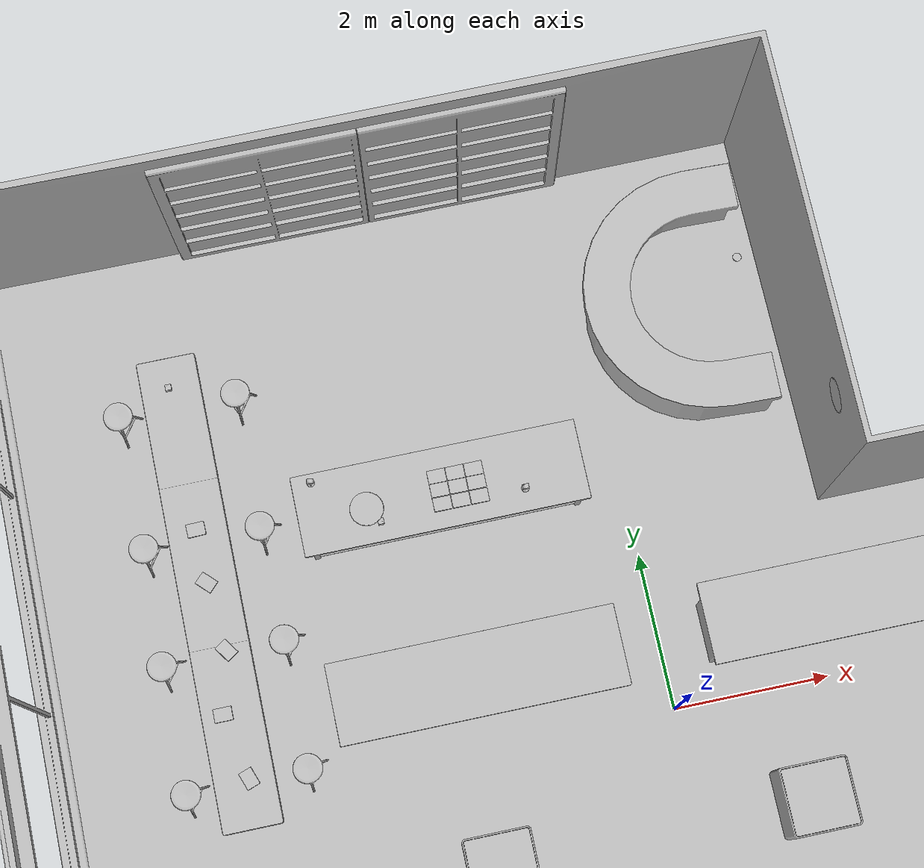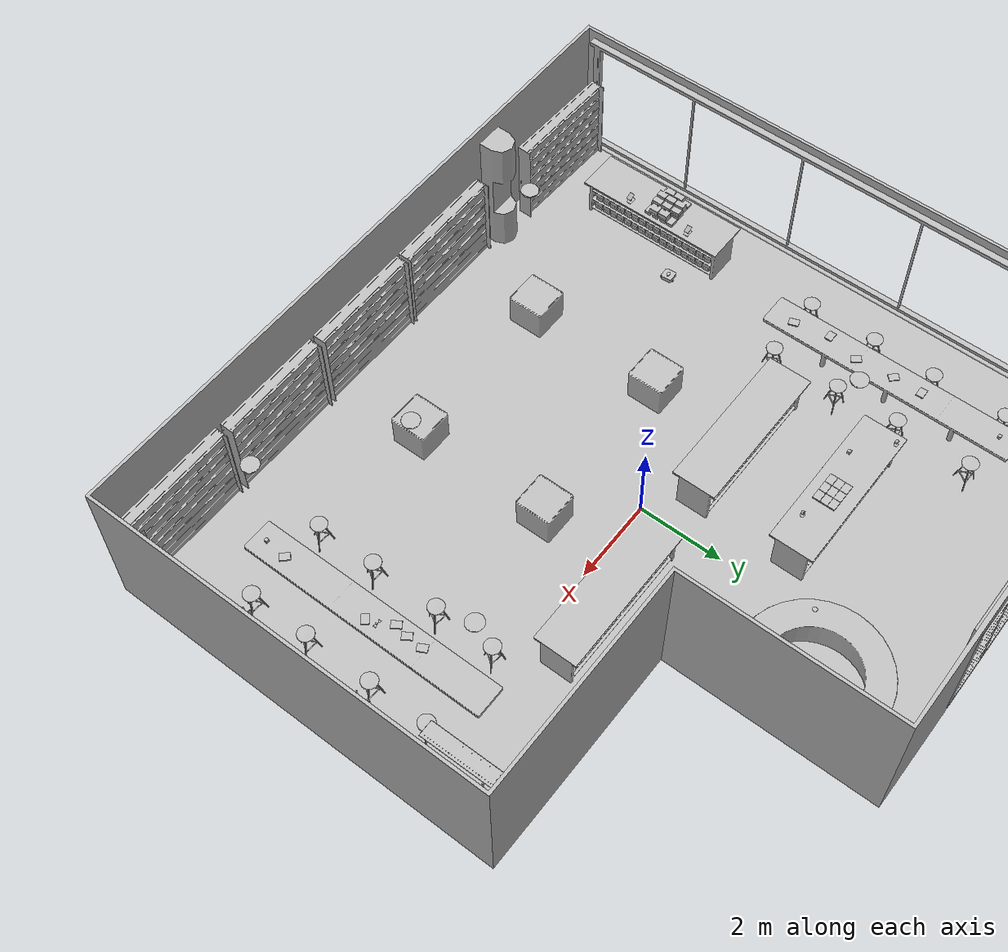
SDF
<sdf version="1.7">
 <world name="default">
  <gravity>0 0 -9.8</gravity>
  <magnetic_field>6e-06 2.3e-05 -4.2e-05</magnetic_field>
  <atmosphere type="adiabatic"/>
  <physics name="default_physics" default="0" type="ode">
   <max_step_size>0.001</max_step_size>
   <real_time_factor>1</real_time_factor>
   <real_time_update_rate>1000</real_time_update_rate>
  </physics>
  <scene>
   <ambient>0.4 0.4 0.4 1</ambient>
   <background>0.7 0.7 0.7 1</background>
   <shadows>1</shadows>
   <grid>0</grid>
   <origin_visual>0</origin_visual>
  </scene>
  <spherical_coordinates>
   <surface_model>EARTH_WGS84</surface_model>
   <latitude_deg>0</latitude_deg>
   <longitude_deg>0</longitude_deg>
   <elevation>0</elevation>
   <heading_deg>0</heading_deg>
  </spherical_coordinates>
  <model name="AirConditionerC_01_001">
   <frame name="aws_robomaker_retail_AirConditionerC_01::__model__" attached_to="aws_robomaker_retail_AirConditionerC_01::link">
    <pose relative_to="__model__">0 0 0 0 -0 0</pose>
   </frame>
   <link name="aws_robomaker_retail_AirConditionerC_01::link">
    <inertial><mass>50</mass></inertial>
    <collision name="collision">
     <geometry>
      <mesh>
       <uri>file://models/aws_robomaker_retail_AirConditionerC_01/meshes/aws_AirConditionerC_01_collision.DAE</uri>
       <scale>1 1 1</scale>
      </mesh>
     </geometry>
    </collision>
    <visual name="visual">
     <geometry>
      <mesh>
       <uri>file://models/aws_robomaker_retail_AirConditionerC_01/meshes/aws_AirConditionerC_01_visual.DAE</uri>
      </mesh>
     </geometry>
     <meta><layer>3</layer></meta>
    </visual>
    <pose relative_to="aws_robomaker_retail_AirConditionerC_01::__model__">0 0 0 0 -0 0</pose>
   </link>
   <static>1</static>
   <pose>7.4582 1.42245 3.29094 0 0 -1.56422</pose>
  </model>
  <model name="Bicycle_01_001">
   <frame name="aws_robomaker_retail_Bicycle_01::__model__" attached_to="aws_robomaker_retail_Bicycle_01::link">
    <pose relative_to="__model__">0 0 0 0 -0 0</pose>
   </frame>
   <link name="aws_robomaker_retail_Bicycle_01::link">
    <inertial>
     <mass>0.04</mass>
     <inertia><ixx>0.1</ixx><ixy>0</ixy><ixz>0</ixz><iyy>0.1</iyy><iyz>0</iyz><izz>0.01</izz></inertia>
    </inertial>
    <collision name="collision">
     <geometry>
      <mesh>
       <uri>file://models/aws_robomaker_retail_Bicycle_01/meshes/aws_Bicycle_01_collision.DAE</uri>
       <scale>1 1 1</scale>
      </mesh>
     </geometry>
    </collision>
    <visual name="visual">
     <geometry>
      <mesh><uri>file://models/aws_robomaker_retail_Bicycle_01/meshes/aws_Bicycle_01_visual.DAE</uri></mesh>
     </geometry>
     <meta><layer>1</layer></meta>
    </visual>
    <pose relative_to="aws_robomaker_retail_Bicycle_01::__model__">0 0 0 0 -0 0</pose>
   </link>
   <static>1</static>
   <pose>5.68125 -2.24245 0.931246 2e-06 -2.4e-05 -0</pose>
  </model>
  <model name="BookE_01_001">
   <frame name="aws_robomaker_retail_BookE_01::__model__" attached_to="aws_robomaker_retail_BookE_01::link">
    <pose relative_to="__model__">0 0 0 0 -0 0</pose>
   </frame>
   <link name="aws_robomaker_retail_BookE_01::link">
    <inertial>
     <mass>1</mass>
     <inertia><ixy>0</ixy><ixz>0</ixz><iyz>0</iyz><ixx>0.0666</ixx><iyy>0.0346</iyy><izz>0.0986</izz></inertia>
    </inertial>
    <collision name="collision">
     <geometry>
      <mesh>
       <uri>file://models/aws_robomaker_retail_BookE_01/meshes/aws_BookE_01_collision.DAE</uri>
       <scale>1 1 1</scale>
      </mesh>
     </geometry>
    </collision>
    <visual name="visual">
     <geometry>
      <mesh><uri>file://models/aws_robomaker_retail_BookE_01/meshes/aws_BookE_01_visual.DAE</uri></mesh>
     </geometry>
     <meta><layer>1</layer></meta>
    </visual>
    <pose relative_to="aws_robomaker_retail_BookE_01::__model__">0 0 0 0 -0 0</pose>
   </link>
   <static>1</static>
   <pose>5.47653 -1.93253 0.948933 4e-06 1e-06 -2.54352</pose>
  </model>
  <model name="BookE_01_002">
   <frame name="aws_robomaker_retail_BookE_01::__model__" attached_to="aws_robomaker_retail_BookE_01::link">
    <pose relative_to="__model__">0 0 0 0 -0 0</pose>
   </frame>
   <link name="aws_robomaker_retail_BookE_01::link">
    <inertial>
     <mass>1</mass>
     <inertia><ixy>0</ixy><ixz>0</ixz><iyz>0</iyz><ixx>0.0666</ixx><iyy>0.0346</iyy><izz>0.0986</izz></inertia>
    </inertial>
    <collision name="collision">
     <geometry>
      <mesh>
       <uri>file://models/aws_robomaker_retail_BookE_01/meshes/aws_BookE_01_collision.DAE</uri>
       <scale>1 1 1</scale>
      </mesh>
     </geometry>
    </collision>
    <visual name="visual">
     <geometry>
      <mesh><uri>file://models/aws_robomaker_retail_BookE_01/meshes/aws_BookE_01_visual.DAE</uri></mesh>
     </geometry>
     <meta><layer>1</layer></meta>
    </visual>
    <pose relative_to="aws_robomaker_retail_BookE_01::__model__">0 0 0 0 -0 0</pose>
   </link>
   <static>1</static>
   <pose>-5.414 3.33067 0.934015 -1e-06 -1e-06 -1.54109</pose>
  </model>
  <model name="BookE_01_003">
   <frame name="aws_robomaker_retail_BookE_01::__model__" attached_to="aws_robomaker_retail_BookE_01::link">
    <pose relative_to="__model__">0 0 0 0 -0 0</pose>
   </frame>
   <link name="aws_robomaker_retail_BookE_01::link">
    <inertial>
     <mass>1</mass>
     <inertia><ixy>0</ixy><ixz>0</ixz><iyz>0</iyz><ixx>0.0666</ixx><iyy>0.0346</iyy><izz>0.0986</izz></inertia>
    </inertial>
    <collision name="collision">
     <geometry>
      <mesh>
       <uri>file://models/aws_robomaker_retail_BookE_01/meshes/aws_BookE_01_collision.DAE</uri>
       <scale>1 1 1</scale>
      </mesh>
     </geometry>
    </collision>
    <visual name="visual">
     <geometry>
      <mesh><uri>file://models/aws_robomaker_retail_BookE_01/meshes/aws_BookE_01_visual.DAE</uri></mesh>
     </geometry>
     <meta><layer>1</layer></meta>
    </visual>
    <pose relative_to="aws_robomaker_retail_BookE_01::__model__">0 0 0 0 -0 0</pose>
   </link>
   <static>1</static>
   <pose>5.55255 -1.21421 0.948933 4e-06 -1e-06 -2.65431</pose>
  </model>
  <model name="BookE_01_004">
   <frame name="aws_robomaker_retail_BookE_01::__model__" attached_to="aws_robomaker_retail_BookE_01::link">
    <pose relative_to="__model__">0 0 0 0 -0 0</pose>
   </frame>
   <link name="aws_robomaker_retail_BookE_01::link">
    <inertial>
     <mass>1</mass>
     <inertia><ixy>0</ixy><ixz>0</ixz><iyz>0</iyz><ixx>0.0666</ixx><iyy>0.0346</iyy><izz>0.0986</izz></inertia>
    </inertial>
    <collision name="collision">
     <geometry>
      <mesh>
       <uri>file://models/aws_robomaker_retail_BookE_01/meshes/aws_BookE_01_collision.DAE</uri>
       <scale>1 1 1</scale>
      </mesh>
     </geometry>
    </collision>
    <visual name="visual">
     <geometry>
      <mesh><uri>file://models/aws_robomaker_retail_BookE_01/meshes/aws_BookE_01_visual.DAE</uri></mesh>
     </geometry>
     <meta><layer>1</layer></meta>
    </visual>
    <pose relative_to="aws_robomaker_retail_BookE_01::__model__">0 0 0 0 -0 0</pose>
   </link>
   <static>1</static>
   <pose>5.67723 -4.6492 0.946394 0.0001 6e-06 -2.35575</pose>
  </model>
  <model name="BookE_01_005">
   <frame name="aws_robomaker_retail_BookE_01::__model__" attached_to="aws_robomaker_retail_BookE_01::link">
    <pose relative_to="__model__">0 0 0 0 -0 0</pose>
   </frame>
   <link name="aws_robomaker_retail_BookE_01::link">
    <inertial>
     <mass>1</mass>
     <inertia><ixy>0</ixy><ixz>0</ixz><iyz>0</iyz><ixx>0.0666</ixx><iyy>0.0346</iyy><izz>0.0986</izz></inertia>
    </inertial>
    <collision name="collision">
     <geometry>
      <mesh>
       <uri>file://models/aws_robomaker_retail_BookE_01/meshes/aws_BookE_01_collision.DAE</uri>
       <scale>1 1 1</scale>
      </mesh>
     </geometry>
    </collision>
    <visual name="visual">
     <geometry>
      <mesh><uri>file://models/aws_robomaker_retail_BookE_01/meshes/aws_BookE_01_visual.DAE</uri></mesh>
     </geometry>
     <meta><layer>1</layer></meta>
    </visual>
    <pose relative_to="aws_robomaker_retail_BookE_01::__model__">0 0 0 0 -0 0</pose>
   </link>
   <static>1</static>
   <pose>5.53815 -1.61032 0.948933 0 0 -2.5269</pose>
  </model>
  <model name="BookE_01_006">
   <frame name="aws_robomaker_retail_BookE_01::__model__" attached_to="aws_robomaker_retail_BookE_01::link">
    <pose relative_to="__model__">0 0 0 0 -0 0</pose>
   </frame>
   <link name="aws_robomaker_retail_BookE_01::link">
    <inertial>
     <mass>1</mass>
     <inertia><ixy>0</ixy><ixz>0</ixz><iyz>0</iyz><ixx>0.0666</ixx><iyy>0.0346</iyy><izz>0.0986</izz></inertia>
    </inertial>
    <collision name="collision">
     <geometry>
      <mesh>
       <uri>file://models/aws_robomaker_retail_BookE_01/meshes/aws_BookE_01_collision.DAE</uri>
       <scale>1 1 1</scale>
      </mesh>
     </geometry>
    </collision>
    <visual name="visual">
     <geometry>
      <mesh><uri>file://models/aws_robomaker_retail_BookE_01/meshes/aws_BookE_01_visual.DAE</uri></mesh>
     </geometry>
     <meta><layer>1</layer></meta>
    </visual>
    <pose relative_to="aws_robomaker_retail_BookE_01::__model__">0 0 0 0 -0 0</pose>
   </link>
   <static>1</static>
   <pose>-1.88942 3.34639 1.05494 0 -0 1.56816</pose>
  </model>
  <model name="BookE_01_007">
   <frame name="aws_robomaker_retail_BookE_01::__model__" attached_to="aws_robomaker_retail_BookE_01::link">
    <pose relative_to="__model__">0 0 0 0 -0 0</pose>
   </frame>
   <link name="aws_robomaker_retail_BookE_01::link">
    <inertial>
     <mass>1</mass>
     <inertia><ixy>0</ixy><ixz>0</ixz><iyz>0</iyz><ixx>0.0666</ixx><iyy>0.0346</iyy><izz>0.0986</izz></inertia>
    </inertial>
    <collision name="collision">
     <geometry>
      <mesh>
       <uri>file://models/aws_robomaker_retail_BookE_01/meshes/aws_BookE_01_collision.DAE</uri>
       <scale>1 1 1</scale>
      </mesh>
     </geometry>
    </collision>
    <visual name="visual">
     <geometry>
      <mesh><uri>file://models/aws_robomaker_retail_BookE_01/meshes/aws_BookE_01_visual.DAE</uri></mesh>
     </geometry>
     <meta><layer>1</layer></meta>
    </visual>
    <pose relative_to="aws_robomaker_retail_BookE_01::__model__">0 0 0 0 -0 0</pose>
   </link>
   <static>1</static>
   <pose>-2.12373 3.34639 1.05494 0 -0 1.56816</pose>
  </model>
  <model name="BookE_01_008">
   <frame name="aws_robomaker_retail_BookE_01::__model__" attached_to="aws_robomaker_retail_BookE_01::link">
    <pose relative_to="__model__">0 0 0 0 -0 0</pose>
   </frame>
   <link name="aws_robomaker_retail_BookE_01::link">
    <inertial>
     <mass>1</mass>
     <inertia><ixy>0</ixy><ixz>0</ixz><iyz>0</iyz><ixx>0.0666</ixx><iyy>0.0346</iyy><izz>0.0986</izz></inertia>
    </inertial>
    <collision name="collision">
     <geometry>
      <mesh>
       <uri>file://models/aws_robomaker_retail_BookE_01/meshes/aws_BookE_01_collision.DAE</uri>
       <scale>1 1 1</scale>
      </mesh>
     </geometry>
    </collision>
    <visual name="visual">
     <geometry>
      <mesh><uri>file://models/aws_robomaker_retail_BookE_01/meshes/aws_BookE_01_visual.DAE</uri></mesh>
     </geometry>
     <meta><layer>1</layer></meta>
    </visual>
    <pose relative_to="aws_robomaker_retail_BookE_01::__model__">0 0 0 0 -0 0</pose>
   </link>
   <static>1</static>
   <pose>-5.31512 1.77195 0.955242 3.14124 -0.072268 -2.52691</pose>
  </model>
  <model name="BookE_01_009">
   <frame name="aws_robomaker_retail_BookE_01::__model__" attached_to="aws_robomaker_retail_BookE_01::link">
    <pose relative_to="__model__">0 0 0 0 -0 0</pose>
   </frame>
   <link name="aws_robomaker_retail_BookE_01::link">
    <inertial>
     <mass>1</mass>
     <inertia><ixy>0</ixy><ixz>0</ixz><iyz>0</iyz><ixx>0.0666</ixx><iyy>0.0346</iyy><izz>0.0986</izz></inertia>
    </inertial>
    <collision name="collision">
     <geometry>
      <mesh>
       <uri>file://models/aws_robomaker_retail_BookE_01/meshes/aws_BookE_01_collision.DAE</uri>
       <scale>1 1 1</scale>
      </mesh>
     </geometry>
    </collision>
    <visual name="visual">
     <geometry>
      <mesh><uri>file://models/aws_robomaker_retail_BookE_01/meshes/aws_BookE_01_visual.DAE</uri></mesh>
     </geometry>
     <meta><layer>1</layer></meta>
    </visual>
    <pose relative_to="aws_robomaker_retail_BookE_01::__model__">0 0 0 0 -0 0</pose>
   </link>
   <static>1</static>
   <pose>1.1702 1.19625 343583 0.002241 -0.0011 -0.623328</pose>
  </model>
  <model name="BookE_01_010">
   <frame name="aws_robomaker_retail_BookE_01::__model__" attached_to="aws_robomaker_retail_BookE_01::link">
    <pose relative_to="__model__">0 0 0 0 -0 0</pose>
   </frame>
   <link name="aws_robomaker_retail_BookE_01::link">
    <inertial>
     <mass>1</mass>
     <inertia><ixy>0</ixy><ixz>0</ixz><iyz>0</iyz><ixx>0.0666</ixx><iyy>0.0346</iyy><izz>0.0986</izz></inertia>
    </inertial>
    <collision name="collision">
     <geometry>
      <mesh>
       <uri>file://models/aws_robomaker_retail_BookE_01/meshes/aws_BookE_01_collision.DAE</uri>
       <scale>1 1 1</scale>
      </mesh>
     </geometry>
    </collision>
    <visual name="visual">
     <geometry>
      <mesh><uri>file://models/aws_robomaker_retail_BookE_01/meshes/aws_BookE_01_visual.DAE</uri></mesh>
     </geometry>
     <meta><layer>1</layer></meta>
    </visual>
    <pose relative_to="aws_robomaker_retail_BookE_01::__model__">0 0 0 0 -0 0</pose>
   </link>
   <static>1</static>
   <pose>-5.50342 1.01206 0.941463 0 0 -1.56844</pose>
  </model>
  <model name="BookE_01_011">
   <frame name="aws_robomaker_retail_BookE_01::__model__" attached_to="aws_robomaker_retail_BookE_01::link">
    <pose relative_to="__model__">0 0 0 0 -0 0</pose>
   </frame>
   <link name="aws_robomaker_retail_BookE_01::link">
    <inertial>
     <mass>1</mass>
     <inertia><ixy>0</ixy><ixz>0</ixz><iyz>0</iyz><ixx>0.0666</ixx><iyy>0.0346</iyy><izz>0.0986</izz></inertia>
    </inertial>
    <collision name="collision">
     <geometry>
      <mesh>
       <uri>file://models/aws_robomaker_retail_BookE_01/meshes/aws_BookE_01_collision.DAE</uri>
       <scale>1 1 1</scale>
      </mesh>
     </geometry>
    </collision>
    <visual name="visual">
     <geometry>
      <mesh><uri>file://models/aws_robomaker_retail_BookE_01/meshes/aws_BookE_01_visual.DAE</uri></mesh>
     </geometry>
     <meta><layer>1</layer></meta>
    </visual>
    <pose relative_to="aws_robomaker_retail_BookE_01::__model__">0 0 0 0 -0 0</pose>
   </link>
   <static>1</static>
   <pose>5.74923 -2.49202 0.948933 2e-06 1e-06 2.22339</pose>
  </model>
  <model name="BookE_01_012">
   <frame name="aws_robomaker_retail_BookE_01::__model__" attached_to="aws_robomaker_retail_BookE_01::link">
    <pose relative_to="__model__">0 0 0 0 -0 0</pose>
   </frame>
   <link name="aws_robomaker_retail_BookE_01::link">
    <inertial>
     <mass>1</mass>
     <inertia><ixy>0</ixy><ixz>0</ixz><iyz>0</iyz><ixx>0.0666</ixx><iyy>0.0346</iyy><izz>0.0986</izz></inertia>
    </inertial>
    <collision name="collision">
     <geometry>
      <mesh>
       <uri>file://models/aws_robomaker_retail_BookE_01/meshes/aws_BookE_01_collision.DAE</uri>
       <scale>1 1 1</scale>
      </mesh>
     </geometry>
    </collision>
    <visual name="visual">
     <geometry>
      <mesh><uri>file://models/aws_robomaker_retail_BookE_01/meshes/aws_BookE_01_visual.DAE</uri></mesh>
     </geometry>
     <meta><layer>1</layer></meta>
    </visual>
    <pose relative_to="aws_robomaker_retail_BookE_01::__model__">0 0 0 0 -0 0</pose>
   </link>
   <static>1</static>
   <pose>-5.33358 0.186186 0.949316 -1e-06 -0.004549 -2.79848</pose>
  </model>
  <model name="BookE_01_013">
   <frame name="aws_robomaker_retail_BookE_01::__model__" attached_to="aws_robomaker_retail_BookE_01::link">
    <pose relative_to="__model__">0 0 0 0 -0 0</pose>
   </frame>
   <link name="aws_robomaker_retail_BookE_01::link">
    <inertial>
     <mass>1</mass>
     <inertia><ixy>0</ixy><ixz>0</ixz><iyz>0</iyz><ixx>0.0666</ixx><iyy>0.0346</iyy><izz>0.0986</izz></inertia>
    </inertial>
    <collision name="collision">
     <geometry>
      <mesh>
       <uri>file://models/aws_robomaker_retail_BookE_01/meshes/aws_BookE_01_collision.DAE</uri>
       <scale>1 1 1</scale>
      </mesh>
     </geometry>
    </collision>
    <visual name="visual">
     <geometry>
      <mesh><uri>file://models/aws_robomaker_retail_BookE_01/meshes/aws_BookE_01_visual.DAE</uri></mesh>
     </geometry>
     <meta><layer>1</layer></meta>
    </visual>
    <pose relative_to="aws_robomaker_retail_BookE_01::__model__">0 0 0 0 -0 0</pose>
   </link>
   <static>1</static>
   <pose>-5.40391 2.65088 0.931119 0.021204 -1e-06 -2.35575</pose>
  </model>
  <model name="BookE_01_014">
   <frame name="aws_robomaker_retail_BookE_01::__model__" attached_to="aws_robomaker_retail_BookE_01::link">
    <pose relative_to="__model__">0 0 0 0 -0 0</pose>
   </frame>
   <link name="aws_robomaker_retail_BookE_01::link">
    <inertial>
     <mass>1</mass>
     <inertia><ixy>0</ixy><ixz>0</ixz><iyz>0</iyz><ixx>0.0666</ixx><iyy>0.0346</iyy><izz>0.0986</izz></inertia>
    </inertial>
    <collision name="collision">
     <geometry>
      <mesh>
       <uri>file://models/aws_robomaker_retail_BookE_01/meshes/aws_BookE_01_collision.DAE</uri>
       <scale>1 1 1</scale>
      </mesh>
     </geometry>
    </collision>
    <visual name="visual">
     <geometry>
      <mesh><uri>file://models/aws_robomaker_retail_BookE_01/meshes/aws_BookE_01_visual.DAE</uri></mesh>
     </geometry>
     <meta><layer>1</layer></meta>
    </visual>
    <pose relative_to="aws_robomaker_retail_BookE_01::__model__">0 0 0 0 -0 0</pose>
   </link>
   <static>1</static>
   <pose>-1.88942 2.99369 1.05494 0 -0 1.56816</pose>
  </model>
  <model name="BookE_01_015">
   <frame name="aws_robomaker_retail_BookE_01::__model__" attached_to="aws_robomaker_retail_BookE_01::link">
    <pose relative_to="__model__">0 0 0 0 -0 0</pose>
   </frame>
   <link name="aws_robomaker_retail_BookE_01::link">
    <inertial>
     <mass>1</mass>
     <inertia><ixy>0</ixy><ixz>0</ixz><iyz>0</iyz><ixx>0.0666</ixx><iyy>0.0346</iyy><izz>0.0986</izz></inertia>
    </inertial>
    <collision name="collision">
     <geometry>
      <mesh>
       <uri>file://models/aws_robomaker_retail_BookE_01/meshes/aws_BookE_01_collision.DAE</uri>
       <scale>1 1 1</scale>
      </mesh>
     </geometry>
    </collision>
    <visual name="visual">
     <geometry>
      <mesh><uri>file://models/aws_robomaker_retail_BookE_01/meshes/aws_BookE_01_visual.DAE</uri></mesh>
     </geometry>
     <meta><layer>1</layer></meta>
    </visual>
    <pose relative_to="aws_robomaker_retail_BookE_01::__model__">0 0 0 0 -0 0</pose>
   </link>
   <static>1</static>
   <pose>-2.12373 2.99369 1.05494 0 -0 1.56816</pose>
  </model>
  <model name="BookE_01_016">
   <frame name="aws_robomaker_retail_BookE_01::__model__" attached_to="aws_robomaker_retail_BookE_01::link">
    <pose relative_to="__model__">0 0 0 0 -0 0</pose>
   </frame>
   <link name="aws_robomaker_retail_BookE_01::link">
    <inertial>
     <mass>1</mass>
     <inertia><ixy>0</ixy><ixz>0</ixz><iyz>0</iyz><ixx>0.0666</ixx><iyy>0.0346</iyy><izz>0.0986</izz></inertia>
    </inertial>
    <collision name="collision">
     <geometry>
      <mesh>
       <uri>file://models/aws_robomaker_retail_BookE_01/meshes/aws_BookE_01_collision.DAE</uri>
       <scale>1 1 1</scale>
      </mesh>
     </geometry>
    </collision>
    <visual name="visual">
     <geometry>
      <mesh><uri>file://models/aws_robomaker_retail_BookE_01/meshes/aws_BookE_01_visual.DAE</uri></mesh>
     </geometry>
     <meta><layer>1</layer></meta>
    </visual>
    <pose relative_to="aws_robomaker_retail_BookE_01::__model__">0 0 0 0 -0 0</pose>
   </link>
   <static>1</static>
   <pose>-2.35737 2.99369 1.05494 0 -0 1.56816</pose>
  </model>
  <model name="BookE_01_017">
   <frame name="aws_robomaker_retail_BookE_01::__model__" attached_to="aws_robomaker_retail_BookE_01::link">
    <pose relative_to="__model__">0 0 0 0 -0 0</pose>
   </frame>
   <link name="aws_robomaker_retail_BookE_01::link">
    <inertial>
     <mass>1</mass>
     <inertia><ixy>0</ixy><ixz>0</ixz><iyz>0</iyz><ixx>0.0666</ixx><iyy>0.0346</iyy><izz>0.0986</izz></inertia>
    </inertial>
    <collision name="collision">
     <geometry>
      <mesh>
       <uri>file://models/aws_robomaker_retail_BookE_01/meshes/aws_BookE_01_collision.DAE</uri>
       <scale>1 1 1</scale>
      </mesh>
     </geometry>
    </collision>
    <visual name="visual">
     <geometry>
      <mesh><uri>file://models/aws_robomaker_retail_BookE_01/meshes/aws_BookE_01_visual.DAE</uri></mesh>
     </geometry>
     <meta><layer>1</layer></meta>
    </visual>
    <pose relative_to="aws_robomaker_retail_BookE_01::__model__">0 0 0 0 -0 0</pose>
   </link>
   <static>1</static>
   <pose>-1.88942 3.17292 1.05494 0 -0 1.56816</pose>
  </model>
  <model name="BookE_01_018">
   <frame name="aws_robomaker_retail_BookE_01::__model__" attached_to="aws_robomaker_retail_BookE_01::link">
    <pose relative_to="__model__">0 0 0 0 -0 0</pose>
   </frame>
   <link name="aws_robomaker_retail_BookE_01::link">
    <inertial>
     <mass>1</mass>
     <inertia><ixy>0</ixy><ixz>0</ixz><iyz>0</iyz><ixx>0.0666</ixx><iyy>0.0346</iyy><izz>0.0986</izz></inertia>
    </inertial>
    <collision name="collision">
     <geometry>
      <mesh>
       <uri>file://models/aws_robomaker_retail_BookE_01/meshes/aws_BookE_01_collision.DAE</uri>
       <scale>1 1 1</scale>
      </mesh>
     </geometry>
    </collision>
    <visual name="visual">
     <geometry>
      <mesh><uri>file://models/aws_robomaker_retail_BookE_01/meshes/aws_BookE_01_visual.DAE</uri></mesh>
     </geometry>
     <meta><layer>1</layer></meta>
    </visual>
    <pose relative_to="aws_robomaker_retail_BookE_01::__model__">0 0 0 0 -0 0</pose>
   </link>
   <static>1</static>
   <pose>-2.12373 3.17292 1.05494 0 -0 1.56816</pose>
  </model>
  <model name="BookE_01_019">
   <frame name="aws_robomaker_retail_BookE_01::__model__" attached_to="aws_robomaker_retail_BookE_01::link">
    <pose relative_to="__model__">0 0 0 0 -0 0</pose>
   </frame>
   <link name="aws_robomaker_retail_BookE_01::link">
    <inertial>
     <mass>1</mass>
     <inertia><ixy>0</ixy><ixz>0</ixz><iyz>0</iyz><ixx>0.0666</ixx><iyy>0.0346</iyy><izz>0.0986</izz></inertia>
    </inertial>
    <collision name="collision">
     <geometry>
      <mesh>
       <uri>file://models/aws_robomaker_retail_BookE_01/meshes/aws_BookE_01_collision.DAE</uri>
       <scale>1 1 1</scale>
      </mesh>
     </geometry>
    </collision>
    <visual name="visual">
     <geometry>
      <mesh><uri>file://models/aws_robomaker_retail_BookE_01/meshes/aws_BookE_01_visual.DAE</uri></mesh>
     </geometry>
     <meta><layer>1</layer></meta>
    </visual>
    <pose relative_to="aws_robomaker_retail_BookE_01::__model__">0 0 0 0 -0 0</pose>
   </link>
   <static>1</static>
   <pose>-2.35737 3.17292 1.05494 0 -0 1.56816</pose>
  </model>
  <model name="BookE_01_030">
   <frame name="aws_robomaker_retail_BookE_01::__model__" attached_to="aws_robomaker_retail_BookE_01::link">
    <pose relative_to="__model__">0 0 0 0 -0 0</pose>
   </frame>
   <link name="aws_robomaker_retail_BookE_01::link">
    <inertial>
     <mass>1</mass>
     <inertia><ixy>0</ixy><ixz>0</ixz><iyz>0</iyz><ixx>0.0666</ixx><iyy>0.0346</iyy><izz>0.0986</izz></inertia>
    </inertial>
    <collision name="collision">
     <geometry>
      <mesh>
       <uri>file://models/aws_robomaker_retail_BookE_01/meshes/aws_BookE_01_collision.DAE</uri>
       <scale>1 1 1</scale>
      </mesh>
     </geometry>
    </collision>
    <visual name="visual">
     <geometry>
      <mesh><uri>file://models/aws_robomaker_retail_BookE_01/meshes/aws_BookE_01_visual.DAE</uri></mesh>
     </geometry>
     <meta><layer>1</layer></meta>
    </visual>
    <pose relative_to="aws_robomaker_retail_BookE_01::__model__">0 0 0 0 -0 0</pose>
   </link>
   <static>1</static>
   <pose>-2.35737 3.34639 1.05494 0 -0 1.56816</pose>
  </model>
  <model name="BookD_01_003">
   <frame name="aws_robomaker_retail_BookD_01::__model__" attached_to="aws_robomaker_retail_BookD_01::link">
    <pose relative_to="__model__">0 0 0 0 -0 0</pose>
   </frame>
   <link name="aws_robomaker_retail_BookD_01::link">
    <inertial><mass>0.5</mass></inertial>
    <collision name="collision">
     <geometry>
      <mesh>
       <uri>file://models/aws_robomaker_retail_BookD_01/meshes/aws_BookD_01_collision.DAE</uri>
       <scale>1 1 1</scale>
      </mesh>
     </geometry>
    </collision>
    <visual name="visual">
     <geometry>
      <mesh><uri>file://models/aws_robomaker_retail_BookD_01/meshes/aws_BookD_01_visual.DAE</uri></mesh>
     </geometry>
     <meta><layer>1</layer></meta>
    </visual>
    <pose relative_to="aws_robomaker_retail_BookD_01::__model__">0 0 0 0 -0 0</pose>
   </link>
   <static>1</static>
   <pose>-6.23561 -3.78518 1.03816 8e-06 -0 1.58038</pose>
  </model>
  <model name="BookshelfB_01_001">
   <frame name="aws_robomaker_retail_BookshelfB_01::__model__" attached_to="aws_robomaker_retail_BookshelfB_01::link">
    <pose relative_to="__model__">0 0 0 0 -0 0</pose>
   </frame>
   <link name="aws_robomaker_retail_BookshelfB_01::link">
    <inertial>
     <mass>50</mass>
     <inertia><ixx>19.8742</ixx><ixy>0</ixy><ixz>0</ixz><iyy>49.1263</iyy><iyz>0</iyz><izz>30.2231</izz></inertia>
    </inertial>
    <collision name="collision">
     <geometry>
      <mesh>
       <uri>file://models/aws_robomaker_retail_BookshelfB_01/meshes/aws_BookshelfB_01_collision.DAE</uri>
       <scale>1 1 1</scale>
      </mesh>
     </geometry>
    </collision>
    <visual name="visual">
     <geometry>
      <mesh><uri>file://models/aws_robomaker_retail_BookshelfB_01/meshes/aws_BookshelfB_01_visual.DAE</uri></mesh>
     </geometry>
     <meta><layer>1</layer></meta>
    </visual>
    <pose relative_to="aws_robomaker_retail_BookshelfB_01::__model__">0 0 0 0 -0 0</pose>
   </link>
   <static>1</static>
   <pose>-6.18968 -6.78565 -0.008942 0.003533 0.000121 -0.032073</pose>
  </model>
  <model name="BookshelfB_01_002">
   <frame name="aws_robomaker_retail_BookshelfB_01::__model__" attached_to="aws_robomaker_retail_BookshelfB_01::link">
    <pose relative_to="__model__">0 0 0 0 -0 0</pose>
   </frame>
   <link name="aws_robomaker_retail_BookshelfB_01::link">
    <inertial>
     <mass>50</mass>
     <inertia><ixx>19.8742</ixx><ixy>0</ixy><ixz>0</ixz><iyy>49.1263</iyy><iyz>0</iyz><izz>30.2231</izz></inertia>
    </inertial>
    <collision name="collision">
     <geometry>
      <mesh>
       <uri>file://models/aws_robomaker_retail_BookshelfB_01/meshes/aws_BookshelfB_01_collision.DAE</uri>
       <scale>1 1 1</scale>
      </mesh>
     </geometry>
    </collision>
    <visual name="visual">
     <geometry>
      <mesh><uri>file://models/aws_robomaker_retail_BookshelfB_01/meshes/aws_BookshelfB_01_visual.DAE</uri></mesh>
     </geometry>
     <meta><layer>1</layer></meta>
    </visual>
    <pose relative_to="aws_robomaker_retail_BookshelfB_01::__model__">0 0 0 0 -0 0</pose>
   </link>
   <static>1</static>
   <pose>-2.20941 -6.97146 0.017074 -0.000128 -0.000252 0.000364</pose>
  </model>
  <model name="BookshelfB_01_003">
   <frame name="aws_robomaker_retail_BookshelfB_01::__model__" attached_to="aws_robomaker_retail_BookshelfB_01::link">
    <pose relative_to="__model__">0 0 0 0 -0 0</pose>
   </frame>
   <link name="aws_robomaker_retail_BookshelfB_01::link">
    <inertial>
     <mass>50</mass>
     <inertia><ixx>19.8742</ixx><ixy>0</ixy><ixz>0</ixz><iyy>49.1263</iyy><iyz>0</iyz><izz>30.2231</izz></inertia>
    </inertial>
    <collision name="collision">
     <geometry>
      <mesh>
       <uri>file://models/aws_robomaker_retail_BookshelfB_01/meshes/aws_BookshelfB_01_collision.DAE</uri>
       <scale>1 1 1</scale>
      </mesh>
     </geometry>
    </collision>
    <visual name="visual">
     <geometry>
      <mesh><uri>file://models/aws_robomaker_retail_BookshelfB_01/meshes/aws_BookshelfB_01_visual.DAE</uri></mesh>
     </geometry>
     <meta><layer>1</layer></meta>
    </visual>
    <pose relative_to="aws_robomaker_retail_BookshelfB_01::__model__">0 0 0 0 -0 0</pose>
   </link>
   <static>1</static>
   <pose>0.522246 -6.9715 0.017947 -0.003292 0 0</pose>
  </model>
  <model name="BookshelfB_01_004">
   <frame name="aws_robomaker_retail_BookshelfB_01::__model__" attached_to="aws_robomaker_retail_BookshelfB_01::link">
    <pose relative_to="__model__">0 0 0 0 -0 0</pose>
   </frame>
   <link name="aws_robomaker_retail_BookshelfB_01::link">
    <inertial>
     <mass>50</mass>
     <inertia><ixx>19.8742</ixx><ixy>0</ixy><ixz>0</ixz><iyy>49.1263</iyy><iyz>0</iyz><izz>30.2231</izz></inertia>
    </inertial>
    <collision name="collision">
     <geometry>
      <mesh>
       <uri>file://models/aws_robomaker_retail_BookshelfB_01/meshes/aws_BookshelfB_01_collision.DAE</uri>
       <scale>1 1 1</scale>
      </mesh>
     </geometry>
    </collision>
    <visual name="visual">
     <geometry>
      <mesh><uri>file://models/aws_robomaker_retail_BookshelfB_01/meshes/aws_BookshelfB_01_visual.DAE</uri></mesh>
     </geometry>
     <meta><layer>1</layer></meta>
    </visual>
    <pose relative_to="aws_robomaker_retail_BookshelfB_01::__model__">0 0 0 0 -0 0</pose>
   </link>
   <static>1</static>
   <pose>3.29339 -6.96366 0.017383 8e-06 -2e-06 -0</pose>
  </model>
  <model name="BookshelfB_01_005">
   <frame name="aws_robomaker_retail_BookshelfB_01::__model__" attached_to="aws_robomaker_retail_BookshelfB_01::link">
    <pose relative_to="__model__">0 0 0 0 -0 0</pose>
   </frame>
   <link name="aws_robomaker_retail_BookshelfB_01::link">
    <inertial>
     <mass>50</mass>
     <inertia><ixx>19.8742</ixx><ixy>0</ixy><ixz>0</ixz><iyy>49.1263</iyy><iyz>0</iyz><izz>30.2231</izz></inertia>
    </inertial>
    <collision name="collision">
     <geometry>
      <mesh>
       <uri>file://models/aws_robomaker_retail_BookshelfB_01/meshes/aws_BookshelfB_01_collision.DAE</uri>
       <scale>1 1 1</scale>
      </mesh>
     </geometry>
    </collision>
    <visual name="visual">
     <geometry>
      <mesh><uri>file://models/aws_robomaker_retail_BookshelfB_01/meshes/aws_BookshelfB_01_visual.DAE</uri></mesh>
     </geometry>
     <meta><layer>1</layer></meta>
    </visual>
    <pose relative_to="aws_robomaker_retail_BookshelfB_01::__model__">0 0 0 0 -0 0</pose>
   </link>
   <static>1</static>
   <pose>6.08038 -6.98766 0.017409 0.000174 4e-06 0</pose>
  </model>
  <model name="BookshelfB_01_006">
   <frame name="aws_robomaker_retail_BookshelfB_01::__model__" attached_to="aws_robomaker_retail_BookshelfB_01::link">
    <pose relative_to="__model__">0 0 0 0 -0 0</pose>
   </frame>
   <link name="aws_robomaker_retail_BookshelfB_01::link">
    <inertial>
     <mass>50</mass>
     <inertia><ixx>19.8742</ixx><ixy>0</ixy><ixz>0</ixz><iyy>49.1263</iyy><iyz>0</iyz><izz>30.2231</izz></inertia>
    </inertial>
    <collision name="collision">
     <geometry>
      <mesh>
       <uri>file://models/aws_robomaker_retail_BookshelfB_01/meshes/aws_BookshelfB_01_collision.DAE</uri>
       <scale>1 1 1</scale>
      </mesh>
     </geometry>
    </collision>
    <visual name="visual">
     <geometry>
      <mesh><uri>file://models/aws_robomaker_retail_BookshelfB_01/meshes/aws_BookshelfB_01_visual.DAE</uri></mesh>
     </geometry>
     <meta><layer>1</layer></meta>
    </visual>
    <pose relative_to="aws_robomaker_retail_BookshelfB_01::__model__">0 0 0 0 -0 0</pose>
   </link>
   <static>1</static>
   <pose>7.47833 -5.2983 0.017443 -0.001974 -0.000211 1.55406</pose>
  </model>
  <model name="BookshelfB_01_007">
   <frame name="aws_robomaker_retail_BookshelfB_01::__model__" attached_to="aws_robomaker_retail_BookshelfB_01::link">
    <pose relative_to="__model__">0 0 0 0 -0 0</pose>
   </frame>
   <link name="aws_robomaker_retail_BookshelfB_01::link">
    <inertial>
     <mass>50</mass>
     <inertia><ixx>19.8742</ixx><ixy>0</ixy><ixz>0</ixz><iyy>49.1263</iyy><iyz>0</iyz><izz>30.2231</izz></inertia>
    </inertial>
    <collision name="collision">
     <geometry>
      <mesh>
       <uri>file://models/aws_robomaker_retail_BookshelfB_01/meshes/aws_BookshelfB_01_collision.DAE</uri>
       <scale>1 1 1</scale>
      </mesh>
     </geometry>
    </collision>
    <visual name="visual">
     <geometry>
      <mesh><uri>file://models/aws_robomaker_retail_BookshelfB_01/meshes/aws_BookshelfB_01_visual.DAE</uri></mesh>
     </geometry>
     <meta><layer>1</layer></meta>
    </visual>
    <pose relative_to="aws_robomaker_retail_BookshelfB_01::__model__">0 0 0 0 -0 0</pose>
   </link>
   <static>1</static>
   <pose>7.47833 -2.51065 0.017402 1e-05 -1.3e-05 1.56207</pose>
  </model>
  <model name="BookshelfB_01_008">
   <frame name="aws_robomaker_retail_BookshelfB_01::__model__" attached_to="aws_robomaker_retail_BookshelfB_01::link">
    <pose relative_to="__model__">0 0 0 0 -0 0</pose>
   </frame>
   <link name="aws_robomaker_retail_BookshelfB_01::link">
    <inertial>
     <mass>50</mass>
     <inertia><ixx>19.8742</ixx><ixy>0</ixy><ixz>0</ixz><iyy>49.1263</iyy><iyz>0</iyz><izz>30.2231</izz></inertia>
    </inertial>
    <collision name="collision">
     <geometry>
      <mesh>
       <uri>file://models/aws_robomaker_retail_BookshelfB_01/meshes/aws_BookshelfB_01_collision.DAE</uri>
       <scale>1 1 1</scale>
      </mesh>
     </geometry>
    </collision>
    <visual name="visual">
     <geometry>
      <mesh><uri>file://models/aws_robomaker_retail_BookshelfB_01/meshes/aws_BookshelfB_01_visual.DAE</uri></mesh>
     </geometry>
     <meta><layer>1</layer></meta>
    </visual>
    <pose relative_to="aws_robomaker_retail_BookshelfB_01::__model__">0 0 0 0 -0 0</pose>
   </link>
   <static>1</static>
   <pose>7.47833 0.402539 0.017181 3e-06 -0.000156 1.5708</pose>
  </model>
  <model name="BookshelfC_01_001">
   <frame name="aws_robomaker_retail_BookshelfC_01::__model__" attached_to="aws_robomaker_retail_BookshelfC_01::link">
    <pose relative_to="__model__">0 0 0 0 -0 0</pose>
   </frame>
   <link name="aws_robomaker_retail_BookshelfC_01::link">
    <inertial>
     <mass>50</mass>
     <inertia><ixx>5.5865</ixx><ixy>0</ixy><ixz>0</ixz><iyy>5.47324</iyy><iyz>0</iyz><izz>6.23277</izz></inertia>
    </inertial>
    <collision name="collision">
     <geometry>
      <mesh>
       <uri>file://models/aws_robomaker_retail_BookshelfC_01/meshes/aws_BookshelfC_01_collision.DAE</uri>
       <scale>1 1 1</scale>
      </mesh>
     </geometry>
    </collision>
    <visual name="visual">
     <geometry>
      <mesh><uri>file://models/aws_robomaker_retail_BookshelfC_01/meshes/aws_BookshelfC_01_visual.DAE</uri></mesh>
     </geometry>
     <meta><layer>1</layer></meta>
    </visual>
    <pose relative_to="aws_robomaker_retail_BookshelfC_01::__model__">0 0 0 0 -0 0</pose>
   </link>
   <static>1</static>
   <pose>1.40515 -1.44974 0.008469 0.003452 -3e-06 0.00062</pose>
  </model>
  <model name="BookshelfC_01_002">
   <frame name="aws_robomaker_retail_BookshelfC_01::__model__" attached_to="aws_robomaker_retail_BookshelfC_01::link">
    <pose relative_to="__model__">0 0 0 0 -0 0</pose>
   </frame>
   <link name="aws_robomaker_retail_BookshelfC_01::link">
    <inertial>
     <mass>50</mass>
     <inertia><ixx>5.5865</ixx><ixy>0</ixy><ixz>0</ixz><iyy>5.47324</iyy><iyz>0</iyz><izz>6.23277</izz></inertia>
    </inertial>
    <collision name="collision">
     <geometry>
      <mesh>
       <uri>file://models/aws_robomaker_retail_BookshelfC_01/meshes/aws_BookshelfC_01_collision.DAE</uri>
       <scale>1 1 1</scale>
      </mesh>
     </geometry>
    </collision>
    <visual name="visual">
     <geometry>
      <mesh><uri>file://models/aws_robomaker_retail_BookshelfC_01/meshes/aws_BookshelfC_01_visual.DAE</uri></mesh>
     </geometry>
     <meta><layer>1</layer></meta>
    </visual>
    <pose relative_to="aws_robomaker_retail_BookshelfC_01::__model__">0 0 0 0 -0 0</pose>
   </link>
   <static>1</static>
   <pose>1.40515 -4.76165 -0.003455 0.003452 -0 1.4e-05</pose>
  </model>
  <model name="BookshelfC_01_003">
   <frame name="aws_robomaker_retail_BookshelfC_01::__model__" attached_to="aws_robomaker_retail_BookshelfC_01::link">
    <pose relative_to="__model__">0 0 0 0 -0 0</pose>
   </frame>
   <link name="aws_robomaker_retail_BookshelfC_01::link">
    <inertial>
     <mass>50</mass>
     <inertia><ixx>5.5865</ixx><ixy>0</ixy><ixz>0</ixz><iyy>5.47324</iyy><iyz>0</iyz><izz>6.23277</izz></inertia>
    </inertial>
    <collision name="collision">
     <geometry>
      <mesh>
       <uri>file://models/aws_robomaker_retail_BookshelfC_01/meshes/aws_BookshelfC_01_collision.DAE</uri>
       <scale>1 1 1</scale>
      </mesh>
     </geometry>
    </collision>
    <visual name="visual">
     <geometry>
      <mesh><uri>file://models/aws_robomaker_retail_BookshelfC_01/meshes/aws_BookshelfC_01_visual.DAE</uri></mesh>
     </geometry>
     <meta><layer>1</layer></meta>
    </visual>
    <pose relative_to="aws_robomaker_retail_BookshelfC_01::__model__">0 0 0 0 -0 0</pose>
   </link>
   <static>1</static>
   <pose>-2.55449 -1.48746 0.045908 0 -0 0</pose>
  </model>
  <model name="BookshelfC_01_004">
   <frame name="aws_robomaker_retail_BookshelfC_01::__model__" attached_to="aws_robomaker_retail_BookshelfC_01::link">
    <pose relative_to="__model__">0 0 0 0 -0 0</pose>
   </frame>
   <link name="aws_robomaker_retail_BookshelfC_01::link">
    <inertial>
     <mass>50</mass>
     <inertia><ixx>5.5865</ixx><ixy>0</ixy><ixz>0</ixz><iyy>5.47324</iyy><iyz>0</iyz><izz>6.23277</izz></inertia>
    </inertial>
    <collision name="collision">
     <geometry>
      <mesh>
       <uri>file://models/aws_robomaker_retail_BookshelfC_01/meshes/aws_BookshelfC_01_collision.DAE</uri>
       <scale>1 1 1</scale>
      </mesh>
     </geometry>
    </collision>
    <visual name="visual">
     <geometry>
      <mesh><uri>file://models/aws_robomaker_retail_BookshelfC_01/meshes/aws_BookshelfC_01_visual.DAE</uri></mesh>
     </geometry>
     <meta><layer>1</layer></meta>
    </visual>
    <pose relative_to="aws_robomaker_retail_BookshelfC_01::__model__">0 0 0 0 -0 0</pose>
   </link>
   <static>1</static>
   <pose>-2.60858 -4.76165 0.045908 0 -0 0</pose>
  </model>
  <model name="ChairB_01_001">
   <frame name="aws_robomaker_retail_ChairB_01::__model__" attached_to="aws_robomaker_retail_ChairB_01::link">
    <pose relative_to="__model__">0 0 0 0 -0 0</pose>
   </frame>
   <link name="aws_robomaker_retail_ChairB_01::link">
    <inertial>
     <mass>3</mass>
     <inertia>
      <ixx>0.188185</ixx>
      <ixy>0</ixy>
      <ixz>0</ixz>
      <iyy>0.190617</iyy>
      <iyz>0</iyz>
      <izz>0.100999</izz>
     </inertia>
    </inertial>
    <collision name="collision">
     <geometry>
      <mesh>
       <uri>file://models/aws_robomaker_retail_ChairB_01/meshes/aws_ChairB_01_collision.DAE</uri>
       <scale>1 1 1</scale>
      </mesh>
     </geometry>
    </collision>
    <visual name="visual">
     <geometry>
      <mesh><uri>file://models/aws_robomaker_retail_ChairB_01/meshes/aws_ChairB_01_visual.DAE</uri></mesh>
     </geometry>
     <meta><layer>1</layer></meta>
    </visual>
    <pose relative_to="aws_robomaker_retail_ChairB_01::__model__">0 0 0 0 -0 0</pose>
   </link>
   <static>1</static>
   <pose>6.64396 -0.210457 0.022051 0 0.006174 8.8e-05</pose>
  </model>
  <model name="ChairB_01_002">
   <frame name="aws_robomaker_retail_ChairB_01::__model__" attached_to="aws_robomaker_retail_ChairB_01::link">
    <pose relative_to="__model__">0 0 0 0 -0 0</pose>
   </frame>
   <link name="aws_robomaker_retail_ChairB_01::link">
    <inertial>
     <mass>3</mass>
     <inertia>
      <ixx>0.188185</ixx>
      <ixy>0</ixy>
      <ixz>0</ixz>
      <iyy>0.190617</iyy>
      <iyz>0</iyz>
      <izz>0.100999</izz>
     </inertia>
    </inertial>
    <collision name="collision">
     <geometry>
      <mesh>
       <uri>file://models/aws_robomaker_retail_ChairB_01/meshes/aws_ChairB_01_collision.DAE</uri>
       <scale>1 1 1</scale>
      </mesh>
     </geometry>
    </collision>
    <visual name="visual">
     <geometry>
      <mesh><uri>file://models/aws_robomaker_retail_ChairB_01/meshes/aws_ChairB_01_visual.DAE</uri></mesh>
     </geometry>
     <meta><layer>1</layer></meta>
    </visual>
    <pose relative_to="aws_robomaker_retail_ChairB_01::__model__">0 0 0 0 -0 0</pose>
   </link>
   <static>1</static>
   <pose>6.64396 -1.62199 0.022051 0 0.006174 8.8e-05</pose>
  </model>
  <model name="ChairB_01_003">
   <frame name="aws_robomaker_retail_ChairB_01::__model__" attached_to="aws_robomaker_retail_ChairB_01::link">
    <pose relative_to="__model__">0 0 0 0 -0 0</pose>
   </frame>
   <link name="aws_robomaker_retail_ChairB_01::link">
    <inertial>
     <mass>3</mass>
     <inertia>
      <ixx>0.188185</ixx>
      <ixy>0</ixy>
      <ixz>0</ixz>
      <iyy>0.190617</iyy>
      <iyz>0</iyz>
      <izz>0.100999</izz>
     </inertia>
    </inertial>
    <collision name="collision">
     <geometry>
      <mesh>
       <uri>file://models/aws_robomaker_retail_ChairB_01/meshes/aws_ChairB_01_collision.DAE</uri>
       <scale>1 1 1</scale>
      </mesh>
     </geometry>
    </collision>
    <visual name="visual">
     <geometry>
      <mesh><uri>file://models/aws_robomaker_retail_ChairB_01/meshes/aws_ChairB_01_visual.DAE</uri></mesh>
     </geometry>
     <meta><layer>1</layer></meta>
    </visual>
    <pose relative_to="aws_robomaker_retail_ChairB_01::__model__">0 0 0 0 -0 0</pose>
   </link>
   <static>1</static>
   <pose>6.64396 -3.24663 0.022051 0 0.006174 8.8e-05</pose>
  </model>
  <model name="ChairB_01_004">
   <frame name="aws_robomaker_retail_ChairB_01::__model__" attached_to="aws_robomaker_retail_ChairB_01::link">
    <pose relative_to="__model__">0 0 0 0 -0 0</pose>
   </frame>
   <link name="aws_robomaker_retail_ChairB_01::link">
    <inertial>
     <mass>3</mass>
     <inertia>
      <ixx>0.188185</ixx>
      <ixy>0</ixy>
      <ixz>0</ixz>
      <iyy>0.190617</iyy>
      <iyz>0</iyz>
      <izz>0.100999</izz>
     </inertia>
    </inertial>
    <collision name="collision">
     <geometry>
      <mesh>
       <uri>file://models/aws_robomaker_retail_ChairB_01/meshes/aws_ChairB_01_collision.DAE</uri>
       <scale>1 1 1</scale>
      </mesh>
     </geometry>
    </collision>
    <visual name="visual">
     <geometry>
      <mesh><uri>file://models/aws_robomaker_retail_ChairB_01/meshes/aws_ChairB_01_visual.DAE</uri></mesh>
     </geometry>
     <meta><layer>1</layer></meta>
    </visual>
    <pose relative_to="aws_robomaker_retail_ChairB_01::__model__">0 0 0 0 -0 0</pose>
   </link>
   <static>1</static>
   <pose>6.64396 -4.6816 0.022051 0 0.006174 8.8e-05</pose>
  </model>
  <model name="ChairB_01_005">
   <frame name="aws_robomaker_retail_ChairB_01::__model__" attached_to="aws_robomaker_retail_ChairB_01::link">
    <pose relative_to="__model__">0 0 0 0 -0 0</pose>
   </frame>
   <link name="aws_robomaker_retail_ChairB_01::link">
    <inertial>
     <mass>3</mass>
     <inertia>
      <ixx>0.188185</ixx>
      <ixy>0</ixy>
      <ixz>0</ixz>
      <iyy>0.190617</iyy>
      <iyz>0</iyz>
      <izz>0.100999</izz>
     </inertia>
    </inertial>
    <collision name="collision">
     <geometry>
      <mesh>
       <uri>file://models/aws_robomaker_retail_ChairB_01/meshes/aws_ChairB_01_collision.DAE</uri>
       <scale>1 1 1</scale>
      </mesh>
     </geometry>
    </collision>
    <visual name="visual">
     <geometry>
      <mesh><uri>file://models/aws_robomaker_retail_ChairB_01/meshes/aws_ChairB_01_visual.DAE</uri></mesh>
     </geometry>
     <meta><layer>1</layer></meta>
    </visual>
    <pose relative_to="aws_robomaker_retail_ChairB_01::__model__">0 0 0 0 -0 0</pose>
   </link>
   <static>1</static>
   <pose>4.6533 -0.210457 0.022051 0 0.006174 8.8e-05</pose>
  </model>
  <model name="ChairB_01_006">
   <frame name="aws_robomaker_retail_ChairB_01::__model__" attached_to="aws_robomaker_retail_ChairB_01::link">
    <pose relative_to="__model__">0 0 0 0 -0 0</pose>
   </frame>
   <link name="aws_robomaker_retail_ChairB_01::link">
    <inertial>
     <mass>3</mass>
     <inertia>
      <ixx>0.188185</ixx>
      <ixy>0</ixy>
      <ixz>0</ixz>
      <iyy>0.190617</iyy>
      <iyz>0</iyz>
      <izz>0.100999</izz>
     </inertia>
    </inertial>
    <collision name="collision">
     <geometry>
      <mesh>
       <uri>file://models/aws_robomaker_retail_ChairB_01/meshes/aws_ChairB_01_collision.DAE</uri>
       <scale>1 1 1</scale>
      </mesh>
     </geometry>
    </collision>
    <visual name="visual">
     <geometry>
      <mesh><uri>file://models/aws_robomaker_retail_ChairB_01/meshes/aws_ChairB_01_visual.DAE</uri></mesh>
     </geometry>
     <meta><layer>1</layer></meta>
    </visual>
    <pose relative_to="aws_robomaker_retail_ChairB_01::__model__">0 0 0 0 -0 0</pose>
   </link>
   <static>1</static>
   <pose>4.6533 -1.62199 0.022051 0 0.006174 8.8e-05</pose>
  </model>
  <model name="ChairB_01_007">
   <frame name="aws_robomaker_retail_ChairB_01::__model__" attached_to="aws_robomaker_retail_ChairB_01::link">
    <pose relative_to="__model__">0 0 0 0 -0 0</pose>
   </frame>
   <link name="aws_robomaker_retail_ChairB_01::link">
    <inertial>
     <mass>3</mass>
     <inertia>
      <ixx>0.188185</ixx>
      <ixy>0</ixy>
      <ixz>0</ixz>
      <iyy>0.190617</iyy>
      <iyz>0</iyz>
      <izz>0.100999</izz>
     </inertia>
    </inertial>
    <collision name="collision">
     <geometry>
      <mesh>
       <uri>file://models/aws_robomaker_retail_ChairB_01/meshes/aws_ChairB_01_collision.DAE</uri>
       <scale>1 1 1</scale>
      </mesh>
     </geometry>
    </collision>
    <visual name="visual">
     <geometry>
      <mesh><uri>file://models/aws_robomaker_retail_ChairB_01/meshes/aws_ChairB_01_visual.DAE</uri></mesh>
     </geometry>
     <meta><layer>1</layer></meta>
    </visual>
    <pose relative_to="aws_robomaker_retail_ChairB_01::__model__">0 0 0 0 -0 0</pose>
   </link>
   <static>1</static>
   <pose>4.6533 -3.24663 0.022051 0 0.006174 8.8e-05</pose>
  </model>
  <model name="ChairB_01_008">
   <frame name="aws_robomaker_retail_ChairB_01::__model__" attached_to="aws_robomaker_retail_ChairB_01::link">
    <pose relative_to="__model__">0 0 0 0 -0 0</pose>
   </frame>
   <link name="aws_robomaker_retail_ChairB_01::link">
    <inertial>
     <mass>3</mass>
     <inertia>
      <ixx>0.188185</ixx>
      <ixy>0</ixy>
      <ixz>0</ixz>
      <iyy>0.190617</iyy>
      <iyz>0</iyz>
      <izz>0.100999</izz>
     </inertia>
    </inertial>
    <collision name="collision">
     <geometry>
      <mesh>
       <uri>file://models/aws_robomaker_retail_ChairB_01/meshes/aws_ChairB_01_collision.DAE</uri>
       <scale>1 1 1</scale>
      </mesh>
     </geometry>
    </collision>
    <visual name="visual">
     <geometry>
      <mesh><uri>file://models/aws_robomaker_retail_ChairB_01/meshes/aws_ChairB_01_visual.DAE</uri></mesh>
     </geometry>
     <meta><layer>1</layer></meta>
    </visual>
    <pose relative_to="aws_robomaker_retail_ChairB_01::__model__">0 0 0 0 -0 0</pose>
   </link>
   <static>1</static>
   <pose>4.6533 -4.6816 0.022051 0 0.006174 8.8e-05</pose>
  </model>
  <model name="ChairB_01_009">
   <frame name="aws_robomaker_retail_ChairB_01::__model__" attached_to="aws_robomaker_retail_ChairB_01::link">
    <pose relative_to="__model__">0 0 0 0 -0 0</pose>
   </frame>
   <link name="aws_robomaker_retail_ChairB_01::link">
    <inertial>
     <mass>3</mass>
     <inertia>
      <ixx>0.188185</ixx>
      <ixy>0</ixy>
      <ixz>0</ixz>
      <iyy>0.190617</iyy>
      <iyz>0</iyz>
      <izz>0.100999</izz>
     </inertia>
    </inertial>
    <collision name="collision">
     <geometry>
      <mesh>
       <uri>file://models/aws_robomaker_retail_ChairB_01/meshes/aws_ChairB_01_collision.DAE</uri>
       <scale>1 1 1</scale>
      </mesh>
     </geometry>
    </collision>
    <visual name="visual">
     <geometry>
      <mesh><uri>file://models/aws_robomaker_retail_ChairB_01/meshes/aws_ChairB_01_visual.DAE</uri></mesh>
     </geometry>
     <meta><layer>1</layer></meta>
    </visual>
    <pose relative_to="aws_robomaker_retail_ChairB_01::__model__">0 0 0 0 -0 0</pose>
   </link>
   <static>1</static>
   <pose>-4.60295 5.02192 0.030259 -0.001073 -0.001935 0.001439</pose>
  </model>
  <model name="ChairB_01_010">
   <frame name="aws_robomaker_retail_ChairB_01::__model__" attached_to="aws_robomaker_retail_ChairB_01::link">
    <pose relative_to="__model__">0 0 0 0 -0 0</pose>
   </frame>
   <link name="aws_robomaker_retail_ChairB_01::link">
    <inertial>
     <mass>3</mass>
     <inertia>
      <ixx>0.188185</ixx>
      <ixy>0</ixy>
      <ixz>0</ixz>
      <iyy>0.190617</iyy>
      <iyz>0</iyz>
      <izz>0.100999</izz>
     </inertia>
    </inertial>
    <collision name="collision">
     <geometry>
      <mesh>
       <uri>file://models/aws_robomaker_retail_ChairB_01/meshes/aws_ChairB_01_collision.DAE</uri>
       <scale>1 1 1</scale>
      </mesh>
     </geometry>
    </collision>
    <visual name="visual">
     <geometry>
      <mesh><uri>file://models/aws_robomaker_retail_ChairB_01/meshes/aws_ChairB_01_visual.DAE</uri></mesh>
     </geometry>
     <meta><layer>1</layer></meta>
    </visual>
    <pose relative_to="aws_robomaker_retail_ChairB_01::__model__">0 0 0 0 -0 0</pose>
   </link>
   <static>1</static>
   <pose>-6.10969 5.02625 0.027274 -0.001422 -0.002424 0.000176</pose>
  </model>
  <model name="ChairB_01_011">
   <frame name="aws_robomaker_retail_ChairB_01::__model__" attached_to="aws_robomaker_retail_ChairB_01::link">
    <pose relative_to="__model__">0 0 0 0 -0 0</pose>
   </frame>
   <link name="aws_robomaker_retail_ChairB_01::link">
    <inertial>
     <mass>3</mass>
     <inertia>
      <ixx>0.188185</ixx>
      <ixy>0</ixy>
      <ixz>0</ixz>
      <iyy>0.190617</iyy>
      <iyz>0</iyz>
      <izz>0.100999</izz>
     </inertia>
    </inertial>
    <collision name="collision">
     <geometry>
      <mesh>
       <uri>file://models/aws_robomaker_retail_ChairB_01/meshes/aws_ChairB_01_collision.DAE</uri>
       <scale>1 1 1</scale>
      </mesh>
     </geometry>
    </collision>
    <visual name="visual">
     <geometry>
      <mesh><uri>file://models/aws_robomaker_retail_ChairB_01/meshes/aws_ChairB_01_visual.DAE</uri></mesh>
     </geometry>
     <meta><layer>1</layer></meta>
    </visual>
    <pose relative_to="aws_robomaker_retail_ChairB_01::__model__">0 0 0 0 -0 0</pose>
   </link>
   <static>1</static>
   <pose>-4.61617 3.27675 0.0321 -0.001068 -0.001938 0.000117</pose>
  </model>
  <model name="ChairB_01_012">
   <frame name="aws_robomaker_retail_ChairB_01::__model__" attached_to="aws_robomaker_retail_ChairB_01::link">
    <pose relative_to="__model__">0 0 0 0 -0 0</pose>
   </frame>
   <link name="aws_robomaker_retail_ChairB_01::link">
    <inertial>
     <mass>3</mass>
     <inertia>
      <ixx>0.188185</ixx>
      <ixy>0</ixy>
      <ixz>0</ixz>
      <iyy>0.190617</iyy>
      <iyz>0</iyz>
      <izz>0.100999</izz>
     </inertia>
    </inertial>
    <collision name="collision">
     <geometry>
      <mesh>
       <uri>file://models/aws_robomaker_retail_ChairB_01/meshes/aws_ChairB_01_collision.DAE</uri>
       <scale>1 1 1</scale>
      </mesh>
     </geometry>
    </collision>
    <visual name="visual">
     <geometry>
      <mesh><uri>file://models/aws_robomaker_retail_ChairB_01/meshes/aws_ChairB_01_visual.DAE</uri></mesh>
     </geometry>
     <meta><layer>1</layer></meta>
    </visual>
    <pose relative_to="aws_robomaker_retail_ChairB_01::__model__">0 0 0 0 -0 0</pose>
   </link>
   <static>1</static>
   <pose>-6.09076 3.29341 0.029216 -0.001072 -0.001936 0.000119</pose>
  </model>
  <model name="ChairB_01_013">
   <frame name="aws_robomaker_retail_ChairB_01::__model__" attached_to="aws_robomaker_retail_ChairB_01::link">
    <pose relative_to="__model__">0 0 0 0 -0 0</pose>
   </frame>
   <link name="aws_robomaker_retail_ChairB_01::link">
    <inertial>
     <mass>3</mass>
     <inertia>
      <ixx>0.188185</ixx>
      <ixy>0</ixy>
      <ixz>0</ixz>
      <iyy>0.190617</iyy>
      <iyz>0</iyz>
      <izz>0.100999</izz>
     </inertia>
    </inertial>
    <collision name="collision">
     <geometry>
      <mesh>
       <uri>file://models/aws_robomaker_retail_ChairB_01/meshes/aws_ChairB_01_collision.DAE</uri>
       <scale>1 1 1</scale>
      </mesh>
     </geometry>
    </collision>
    <visual name="visual">
     <geometry>
      <mesh><uri>file://models/aws_robomaker_retail_ChairB_01/meshes/aws_ChairB_01_visual.DAE</uri></mesh>
     </geometry>
     <meta><layer>1</layer></meta>
    </visual>
    <pose relative_to="aws_robomaker_retail_ChairB_01::__model__">0 0 0 0 -0 0</pose>
   </link>
   <static>1</static>
   <pose>-4.5896 1.81577 0.032459 0.001362 -0.001944 0.000145</pose>
  </model>
  <model name="ChairB_01_014">
   <frame name="aws_robomaker_retail_ChairB_01::__model__" attached_to="aws_robomaker_retail_ChairB_01::link">
    <pose relative_to="__model__">0 0 0 0 -0 0</pose>
   </frame>
   <link name="aws_robomaker_retail_ChairB_01::link">
    <inertial>
     <mass>3</mass>
     <inertia>
      <ixx>0.188185</ixx>
      <ixy>0</ixy>
      <ixz>0</ixz>
      <iyy>0.190617</iyy>
      <iyz>0</iyz>
      <izz>0.100999</izz>
     </inertia>
    </inertial>
    <collision name="collision">
     <geometry>
      <mesh>
       <uri>file://models/aws_robomaker_retail_ChairB_01/meshes/aws_ChairB_01_collision.DAE</uri>
       <scale>1 1 1</scale>
      </mesh>
     </geometry>
    </collision>
    <visual name="visual">
     <geometry>
      <mesh><uri>file://models/aws_robomaker_retail_ChairB_01/meshes/aws_ChairB_01_visual.DAE</uri></mesh>
     </geometry>
     <meta><layer>1</layer></meta>
    </visual>
    <pose relative_to="aws_robomaker_retail_ChairB_01::__model__">0 0 0 0 -0 0</pose>
   </link>
   <static>1</static>
   <pose>-6.1301 1.7986 0.02944 0.001362 -0.001946 0.000105</pose>
  </model>
  <model name="ChairB_01_015">
   <frame name="aws_robomaker_retail_ChairB_01::__model__" attached_to="aws_robomaker_retail_ChairB_01::link">
    <pose relative_to="__model__">0 0 0 0 -0 0</pose>
   </frame>
   <link name="aws_robomaker_retail_ChairB_01::link">
    <inertial>
     <mass>3</mass>
     <inertia>
      <ixx>0.188185</ixx>
      <ixy>0</ixy>
      <ixz>0</ixz>
      <iyy>0.190617</iyy>
      <iyz>0</iyz>
      <izz>0.100999</izz>
     </inertia>
    </inertial>
    <collision name="collision">
     <geometry>
      <mesh>
       <uri>file://models/aws_robomaker_retail_ChairB_01/meshes/aws_ChairB_01_collision.DAE</uri>
       <scale>1 1 1</scale>
      </mesh>
     </geometry>
    </collision>
    <visual name="visual">
     <geometry>
      <mesh><uri>file://models/aws_robomaker_retail_ChairB_01/meshes/aws_ChairB_01_visual.DAE</uri></mesh>
     </geometry>
     <meta><layer>1</layer></meta>
    </visual>
    <pose relative_to="aws_robomaker_retail_ChairB_01::__model__">0 0 0 0 -0 0</pose>
   </link>
   <static>1</static>
   <pose>-4.6075 0.203637 0.030218 0.001362 -0.001944 0.000163</pose>
  </model>
  <model name="ChairB_01_016">
   <frame name="aws_robomaker_retail_ChairB_01::__model__" attached_to="aws_robomaker_retail_ChairB_01::link">
    <pose relative_to="__model__">0 0 0 0 -0 0</pose>
   </frame>
   <link name="aws_robomaker_retail_ChairB_01::link">
    <inertial>
     <mass>3</mass>
     <inertia>
      <ixx>0.188185</ixx>
      <ixy>0</ixy>
      <ixz>0</ixz>
      <iyy>0.190617</iyy>
      <iyz>0</iyz>
      <izz>0.100999</izz>
     </inertia>
    </inertial>
    <collision name="collision">
     <geometry>
      <mesh>
       <uri>file://models/aws_robomaker_retail_ChairB_01/meshes/aws_ChairB_01_collision.DAE</uri>
       <scale>1 1 1</scale>
      </mesh>
     </geometry>
    </collision>
    <visual name="visual">
     <geometry>
      <mesh><uri>file://models/aws_robomaker_retail_ChairB_01/meshes/aws_ChairB_01_visual.DAE</uri></mesh>
     </geometry>
     <meta><layer>1</layer></meta>
    </visual>
    <pose relative_to="aws_robomaker_retail_ChairB_01::__model__">0 0 0 0 -0 0</pose>
   </link>
   <static>1</static>
   <pose>-6.12149 0.195027 0.027272 0.001357 -0.00195 0.003291</pose>
  </model>
  <model name="ColumnB_01_002">
   <frame name="aws_robomaker_retail_ColumnB_01::__model__" attached_to="aws_robomaker_retail_ColumnB_01::link">
    <pose relative_to="__model__">0 0 0 0 -0 0</pose>
   </frame>
   <link name="aws_robomaker_retail_ColumnB_01::link">
    <inertial>
     <mass>50</mass>
     <inertia><ixx>44.5597</ixx><ixy>0</ixy><ixz>0</ixz><iyy>44.5597</iyy><iyz>0</iyz><izz>1.87942</izz></inertia>
    </inertial>
    <collision name="collision">
     <geometry>
      <mesh>
       <uri>file://models/aws_robomaker_retail_ColumnB_01/meshes/aws_ColumnB_01_collision.DAE</uri>
       <scale>1 1 1</scale>
      </mesh>
     </geometry>
    </collision>
    <visual name="visual">
     <geometry>
      <mesh><uri>file://models/aws_robomaker_retail_ColumnB_01/meshes/aws_ColumnB_01_visual.DAE</uri></mesh>
     </geometry>
     <meta><layer>1</layer></meta>
    </visual>
    <pose relative_to="aws_robomaker_retail_ColumnB_01::__model__">0 0 0 0 -0 0</pose>
   </link>
   <static>1</static>
   <pose>-4.07623 -6.86071 0.017511 0.001895 -0.000628 -0.003755</pose>
  </model>
  <model name="SecurityCamera_01_001">
   <frame name="aws_robomaker_retail_SecurityCamera_01::__model__" attached_to="aws_robomaker_retail_SecurityCamera_01::link">
    <pose relative_to="__model__">0 0 0 0 -0 0</pose>
   </frame>
   <link name="aws_robomaker_retail_SecurityCamera_01::link">
    <inertial>
     <mass>1</mass>
     <inertia>
      <ixx>18.2222</ixx>
      <ixy>0</ixy>
      <ixz>0</ixz>
      <iyy>18.2222</iyy>
      <iyz>0</iyz>
      <izz>0.0018767</izz>
     </inertia>
    </inertial>
    <collision name="collision">
     <geometry>
      <mesh>
       <uri>file://models/aws_robomaker_retail_SecurityCamera_01/meshes/aws_SecurityCamera_01_collision.DAE</uri>
       <scale>1 1 1</scale>
      </mesh>
     </geometry>
    </collision>
    <visual name="visual">
     <geometry>
      <mesh>
       <uri>file://models/aws_robomaker_retail_SecurityCamera_01/meshes/aws_SecurityCamera_01_visual.DAE</uri>
      </mesh>
     </geometry>
     <meta><layer>2</layer></meta>
    </visual>
    <pose relative_to="aws_robomaker_retail_SecurityCamera_01::__model__">0 0 0 0 -0 0</pose>
   </link>
   <static>1</static>
   <pose>-1.30881 2.97371 1.03776 -0.004006 -9.7e-05 -0.01066</pose>
  </model>
  <model name="SecurityCamera_01_002">
   <frame name="aws_robomaker_retail_SecurityCamera_01::__model__" attached_to="aws_robomaker_retail_SecurityCamera_01::link">
    <pose relative_to="__model__">0 0 0 0 -0 0</pose>
   </frame>
   <link name="aws_robomaker_retail_SecurityCamera_01::link">
    <inertial>
     <mass>1</mass>
     <inertia>
      <ixx>18.2222</ixx>
      <ixy>0</ixy>
      <ixz>0</ixz>
      <iyy>18.2222</iyy>
      <iyz>0</iyz>
      <izz>0.0018767</izz>
     </inertia>
    </inertial>
    <collision name="collision">
     <geometry>
      <mesh>
       <uri>file://models/aws_robomaker_retail_SecurityCamera_01/meshes/aws_SecurityCamera_01_collision.DAE</uri>
       <scale>1 1 1</scale>
      </mesh>
     </geometry>
    </collision>
    <visual name="visual">
     <geometry>
      <mesh>
       <uri>file://models/aws_robomaker_retail_SecurityCamera_01/meshes/aws_SecurityCamera_01_visual.DAE</uri>
      </mesh>
     </geometry>
     <meta><layer>2</layer></meta>
    </visual>
    <pose relative_to="aws_robomaker_retail_SecurityCamera_01::__model__">0 0 0 0 -0 0</pose>
   </link>
   <static>1</static>
   <pose>-3.90451 3.59053 1.03776 0 -0 3.05091</pose>
  </model>
  <model name="InfoDesk_01_001">
   <frame name="aws_robomaker_retail_InfoDesk_01::__model__" attached_to="aws_robomaker_retail_InfoDesk_01::link">
    <pose relative_to="__model__">0 0 0 0 -0 0</pose>
   </frame>
   <link name="aws_robomaker_retail_InfoDesk_01::link">
    <inertial>
     <mass>50</mass>
     <inertia><ixx>47.8386</ixx><ixy>0</ixy><ixz>0</ixz><iyy>25.3705</iyy><iyz>0</iyz><izz>63.5798</izz></inertia>
    </inertial>
    <collision name="collision">
     <geometry>
      <mesh>
       <uri>file://models/aws_robomaker_retail_InfoDesk_01/meshes/aws_InfoDesk_01_collision.DAE</uri>
       <scale>1 1 1</scale>
      </mesh>
     </geometry>
    </collision>
    <visual name="visual">
     <geometry>
      <mesh><uri>file://models/aws_robomaker_retail_InfoDesk_01/meshes/aws_InfoDesk_01_visual.DAE</uri></mesh>
     </geometry>
     <meta><layer>1</layer></meta>
    </visual>
    <pose relative_to="aws_robomaker_retail_InfoDesk_01::__model__">0 0 0 0 -0 0</pose>
   </link>
   <static>1</static>
   <pose>1.01067 5.03258 0.011585 -0.006739 0.00511 -0.025146</pose>
  </model>
  <model name="DeskB_01_001">
   <frame name="aws_robomaker_retail_DeskB_01::__model__" attached_to="aws_robomaker_retail_DeskB_01::link">
    <pose relative_to="__model__">0 0 0 0 -0 0</pose>
   </frame>
   <link name="aws_robomaker_retail_DeskB_01::link">
    <inertial>
     <mass>50</mass>
     <inertia><ixx>154.884</ixx><ixy>0</ixy><ixz>0</ixz><iyy>7.48424</iyy><iyz>0</iyz><izz>152.099</izz></inertia>
    </inertial>
    <collision name="collision">
     <geometry>
      <mesh>
       <uri>file://models/aws_robomaker_retail_DeskB_01/meshes/aws_DeskB_01_collision.DAE</uri>
       <scale>1 1 1</scale>
      </mesh>
     </geometry>
    </collision>
    <visual name="visual">
     <geometry>
      <mesh><uri>file://models/aws_robomaker_retail_DeskB_01/meshes/aws_DeskB_01_visual.DAE</uri></mesh>
     </geometry>
     <meta><layer>1</layer></meta>
    </visual>
    <pose relative_to="aws_robomaker_retail_DeskB_01::__model__">0 0 0 0 -0 0</pose>
   </link>
   <static>1</static>
   <pose>5.62294 -2.47542 -0.181282 0 -0 0</pose>
  </model>
  <model name="DeskB_01_002">
   <frame name="aws_robomaker_retail_DeskB_01::__model__" attached_to="aws_robomaker_retail_DeskB_01::link">
    <pose relative_to="__model__">0 0 0 0 -0 0</pose>
   </frame>
   <link name="aws_robomaker_retail_DeskB_01::link">
    <inertial>
     <mass>50</mass>
     <inertia><ixx>154.884</ixx><ixy>0</ixy><ixz>0</ixz><iyy>7.48424</iyy><iyz>0</iyz><izz>152.099</izz></inertia>
    </inertial>
    <collision name="collision">
     <geometry>
      <mesh>
       <uri>file://models/aws_robomaker_retail_DeskB_01/meshes/aws_DeskB_01_collision.DAE</uri>
       <scale>1 1 1</scale>
      </mesh>
     </geometry>
    </collision>
    <visual name="visual">
     <geometry>
      <mesh><uri>file://models/aws_robomaker_retail_DeskB_01/meshes/aws_DeskB_01_visual.DAE</uri></mesh>
     </geometry>
     <meta><layer>1</layer></meta>
    </visual>
    <pose relative_to="aws_robomaker_retail_DeskB_01::__model__">0 0 0 0 -0 0</pose>
   </link>
   <static>1</static>
   <pose>-5.40071 2.58054 -0.181282 0 -0 0</pose>
  </model>
  <model name="DeskA_01_001">
   <frame name="aws_robomaker_retail_DeskA_01::__model__" attached_to="aws_robomaker_retail_DeskA_01::link">
    <pose relative_to="__model__">0 0 0 0 -0 0</pose>
   </frame>
   <link name="aws_robomaker_retail_DeskA_01::link">
    <inertial>
     <mass>20</mass>
     <inertia><ixx>3.49717</ixx><ixy>0</ixy><ixz>0</ixz><iyy>23.5599</iyy><iyz>0</iyz><izz>23.5702</izz></inertia>
    </inertial>
    <collision name="collision">
     <geometry>
      <mesh>
       <uri>file://models/aws_robomaker_retail_DeskA_01/meshes/aws_DeskA_01_collision.DAE</uri>
       <scale>1 1 1</scale>
      </mesh>
     </geometry>
    </collision>
    <visual name="visual">
     <geometry>
      <mesh><uri>file://models/aws_robomaker_retail_DeskA_01/meshes/aws_DeskA_01_visual.DAE</uri></mesh>
     </geometry>
     <meta><layer>1</layer></meta>
    </visual>
    <pose relative_to="aws_robomaker_retail_DeskA_01::__model__">0 0 0 0 -0 0</pose>
   </link>
   <static>1</static>
   <pose>-2.34069 3.20012 0.014921 0.000124 -1e-05 0.000376</pose>
  </model>
  <model name="DeskA_01_002">
   <frame name="aws_robomaker_retail_DeskA_01::__model__" attached_to="aws_robomaker_retail_DeskA_01::link">
    <pose relative_to="__model__">0 0 0 0 -0 0</pose>
   </frame>
   <link name="aws_robomaker_retail_DeskA_01::link">
    <inertial>
     <mass>20</mass>
     <inertia><ixx>3.49717</ixx><ixy>0</ixy><ixz>0</ixz><iyy>23.5599</iyy><iyz>0</iyz><izz>23.5702</izz></inertia>
    </inertial>
    <collision name="collision">
     <geometry>
      <mesh>
       <uri>file://models/aws_robomaker_retail_DeskA_01/meshes/aws_DeskA_01_collision.DAE</uri>
       <scale>1 1 1</scale>
      </mesh>
     </geometry>
    </collision>
    <visual name="visual">
     <geometry>
      <mesh><uri>file://models/aws_robomaker_retail_DeskA_01/meshes/aws_DeskA_01_visual.DAE</uri></mesh>
     </geometry>
     <meta><layer>1</layer></meta>
    </visual>
    <pose relative_to="aws_robomaker_retail_DeskA_01::__model__">0 0 0 0 -0 0</pose>
   </link>
   <static>1</static>
   <pose>-2.36994 0.836099 0.00876 -0.000772 -0.001938 1.7e-05</pose>
  </model>
  <model name="DeskA_01_003">
   <frame name="aws_robomaker_retail_DeskA_01::__model__" attached_to="aws_robomaker_retail_DeskA_01::link">
    <pose relative_to="__model__">0 0 0 0 -0 0</pose>
   </frame>
   <link name="aws_robomaker_retail_DeskA_01::link">
    <inertial>
     <mass>20</mass>
     <inertia><ixx>3.49717</ixx><ixy>0</ixy><ixz>0</ixz><iyy>23.5599</iyy><iyz>0</iyz><izz>23.5702</izz></inertia>
    </inertial>
    <collision name="collision">
     <geometry>
      <mesh>
       <uri>file://models/aws_robomaker_retail_DeskA_01/meshes/aws_DeskA_01_collision.DAE</uri>
       <scale>1 1 1</scale>
      </mesh>
     </geometry>
    </collision>
    <visual name="visual">
     <geometry>
      <mesh><uri>file://models/aws_robomaker_retail_DeskA_01/meshes/aws_DeskA_01_visual.DAE</uri></mesh>
     </geometry>
     <meta><layer>1</layer></meta>
    </visual>
    <pose relative_to="aws_robomaker_retail_DeskA_01::__model__">0 0 0 0 -0 0</pose>
   </link>
   <static>1</static>
   <pose>-6.25465 -3.9792 -0.004603 0.001948 0.001361 -1.56957</pose>
  </model>
  <model name="DeskA_01_005">
   <frame name="aws_robomaker_retail_DeskA_01::__model__" attached_to="aws_robomaker_retail_DeskA_01::link">
    <pose relative_to="__model__">0 0 0 0 -0 0</pose>
   </frame>
   <link name="aws_robomaker_retail_DeskA_01::link">
    <inertial>
     <mass>20</mass>
     <inertia><ixx>3.49717</ixx><ixy>0</ixy><ixz>0</ixz><iyy>23.5599</iyy><iyz>0</iyz><izz>23.5702</izz></inertia>
    </inertial>
    <collision name="collision">
     <geometry>
      <mesh>
       <uri>file://models/aws_robomaker_retail_DeskA_01/meshes/aws_DeskA_01_collision.DAE</uri>
       <scale>1 1 1</scale>
      </mesh>
     </geometry>
    </collision>
    <visual name="visual">
     <geometry>
      <mesh><uri>file://models/aws_robomaker_retail_DeskA_01/meshes/aws_DeskA_01_visual.DAE</uri></mesh>
     </geometry>
     <meta><layer>1</layer></meta>
    </visual>
    <pose relative_to="aws_robomaker_retail_DeskA_01::__model__">0 0 0 0 -0 0</pose>
   </link>
   <static>1</static>
   <pose>2.2982 0.861754 0.014883 -2e-06 0.003451 2.4e-05</pose>
  </model>
  <model name="DoorB_01_001">
   <frame name="aws_robomaker_retail_DoorB_01::__model__" attached_to="aws_robomaker_retail_DoorB_01::link">
    <pose relative_to="__model__">0 0 0 0 -0 0</pose>
   </frame>
   <link name="aws_robomaker_retail_DoorB_01::link">
    <inertial>
     <mass>50</mass>
     <inertia><ixx>44.5597</ixx><ixy>0</ixy><ixz>0</ixz><iyy>151.699</iyy><iyz>0</iyz><izz>107.806</izz></inertia>
    </inertial>
    <collision name="collision">
     <geometry>
      <mesh>
       <uri>file://models/aws_robomaker_retail_DoorB_01/meshes/aws_DoorB_01_collision.DAE</uri>
       <scale>1 1 1</scale>
      </mesh>
     </geometry>
    </collision>
    <visual name="visual">
     <geometry>
      <mesh><uri>file://models/aws_robomaker_retail_DoorB_01/meshes/aws_DoorB_01_visual.DAE</uri></mesh>
     </geometry>
     <meta><layer>2</layer></meta>
    </visual>
    <pose relative_to="aws_robomaker_retail_DoorB_01::__model__">0 0 0 0 -0 0</pose>
   </link>
   <static>1</static>
   <pose>-2.49246 7.21937 -0.035203 0 -0 0</pose>
  </model>
  <model name="RetailShopFloor_01_001">
   <frame name="aws_robomaker_retail_RetailShopFloor_01::__model__" attached_to="aws_robomaker_retail_RetailShopFloor_01::link">
    <pose relative_to="__model__">0 0 0 0 -0 0</pose>
   </frame>
   <link name="aws_robomaker_retail_RetailShopFloor_01::link">
    <inertial><mass>100</mass></inertial>
    <collision name="collision">
     <geometry>
      <mesh>
       <uri>file://models/aws_robomaker_retail_RetailShopFloor_01/meshes/aws_RetailShopFloor_01_collision.DAE</uri>
       <scale>1 1 1</scale>
      </mesh>
     </geometry>
     <surface><friction><ode><mu>100</mu><mu2>50</mu2></ode></friction></surface>
    </collision>
    <visual name="visual">
     <geometry>
      <mesh>
       <uri>file://models/aws_robomaker_retail_RetailShopFloor_01/meshes/aws_RetailShopFloor_01_visual.DAE</uri>
      </mesh>
     </geometry>
     <meta><layer>1</layer></meta>
    </visual>
    <pose relative_to="aws_robomaker_retail_RetailShopFloor_01::__model__">0 0 0 0 -0 0</pose>
   </link>
   <static>1</static>
   <pose>-0.002687 0 -0.276618 0 -0 0</pose>
  </model>
  <model name="TabletB_01_011">
   <frame name="aws_robomaker_retail_TabletB_01::__model__" attached_to="aws_robomaker_retail_TabletB_01::link">
    <pose relative_to="__model__">0 0 0 0 -0 0</pose>
   </frame>
   <link name="aws_robomaker_retail_TabletB_01::link">
    <inertial>
     <mass>0.161</mass>
     <inertia>
      <ixx>0.346954</ixx>
      <ixy>0</ixy>
      <ixz>0</ixz>
      <iyy>0.177288</iyy>
      <iyz>0</iyz>
      <izz>0.521826</izz>
     </inertia>
    </inertial>
    <collision name="collision">
     <geometry>
      <mesh>
       <uri>file://models/aws_robomaker_retail_TabletB_01/meshes/aws_TabletB_01_collision.DAE</uri>
       <scale>1 1 1</scale>
      </mesh>
     </geometry>
    </collision>
    <visual name="visual">
     <geometry>
      <mesh><uri>file://models/aws_robomaker_retail_TabletB_01/meshes/aws_TabletB_01_visual.DAE</uri></mesh>
     </geometry>
     <meta><layer>1</layer></meta>
    </visual>
    <pose relative_to="aws_robomaker_retail_TabletB_01::__model__">0 0 0 0 -0 0</pose>
   </link>
   <static>1</static>
   <pose>-5.91505 -3.03174 1.18472 0.518384 0.023341 1.56451</pose>
  </model>
  <model name="TabletB_01_012">
   <frame name="aws_robomaker_retail_TabletB_01::__model__" attached_to="aws_robomaker_retail_TabletB_01::link">
    <pose relative_to="__model__">0 0 0 0 -0 0</pose>
   </frame>
   <link name="aws_robomaker_retail_TabletB_01::link">
    <inertial>
     <mass>0.161</mass>
     <inertia>
      <ixx>0.346954</ixx>
      <ixy>0</ixy>
      <ixz>0</ixz>
      <iyy>0.177288</iyy>
      <iyz>0</iyz>
      <izz>0.521826</izz>
     </inertia>
    </inertial>
    <collision name="collision">
     <geometry>
      <mesh>
       <uri>file://models/aws_robomaker_retail_TabletB_01/meshes/aws_TabletB_01_collision.DAE</uri>
       <scale>1 1 1</scale>
      </mesh>
     </geometry>
    </collision>
    <visual name="visual">
     <geometry>
      <mesh><uri>file://models/aws_robomaker_retail_TabletB_01/meshes/aws_TabletB_01_visual.DAE</uri></mesh>
     </geometry>
     <meta><layer>1</layer></meta>
    </visual>
    <pose relative_to="aws_robomaker_retail_TabletB_01::__model__">0 0 0 0 -0 0</pose>
   </link>
   <static>1</static>
   <pose>-5.91505 -4.6124 1.18472 0.518384 0.023341 1.56451</pose>
  </model>
  <model name="Holder_01_019">
   <frame name="aws_robomaker_retail_Holder_01::__model__" attached_to="aws_robomaker_retail_Holder_01::link">
    <pose relative_to="__model__">0 0 0 0 -0 0</pose>
   </frame>
   <link name="aws_robomaker_retail_Holder_01::link">
    <inertial><mass>1</mass></inertial>
    <collision name="collision">
     <geometry>
      <mesh>
       <uri>file://models/aws_robomaker_retail_Holder_01/meshes/aws_Holder_01_collision.DAE</uri>
       <scale>1 1 1</scale>
      </mesh>
     </geometry>
    </collision>
    <visual name="visual">
     <geometry>
      <mesh><uri>file://models/aws_robomaker_retail_Holder_01/meshes/aws_Holder_01_visual.DAE</uri></mesh>
     </geometry>
     <meta><layer>2</layer></meta>
    </visual>
    <pose relative_to="aws_robomaker_retail_Holder_01::__model__">0 0 0 0 -0 0</pose>
   </link>
   <static>1</static>
   <pose>-5.92911 -3.03279 1.03776 0 -0 1.55</pose>
  </model>
  <model name="Holder_01_020">
   <frame name="aws_robomaker_retail_Holder_01::__model__" attached_to="aws_robomaker_retail_Holder_01::link">
    <pose relative_to="__model__">0 0 0 0 -0 0</pose>
   </frame>
   <link name="aws_robomaker_retail_Holder_01::link">
    <inertial><mass>1</mass></inertial>
    <collision name="collision">
     <geometry>
      <mesh>
       <uri>file://models/aws_robomaker_retail_Holder_01/meshes/aws_Holder_01_collision.DAE</uri>
       <scale>1 1 1</scale>
      </mesh>
     </geometry>
    </collision>
    <visual name="visual">
     <geometry>
      <mesh><uri>file://models/aws_robomaker_retail_Holder_01/meshes/aws_Holder_01_visual.DAE</uri></mesh>
     </geometry>
     <meta><layer>2</layer></meta>
    </visual>
    <pose relative_to="aws_robomaker_retail_Holder_01::__model__">0 0 0 0 -0 0</pose>
   </link>
   <static>1</static>
   <pose>-5.92911 -4.60364 1.03776 0 -0 1.55</pose>
  </model>
  <model name="Horologe_01_001">
   <frame name="aws_robomaker_retail_Horologe_01::__model__" attached_to="aws_robomaker_retail_Horologe_01::link">
    <pose relative_to="__model__">0 0 0 0 -0 0</pose>
   </frame>
   <link name="aws_robomaker_retail_Horologe_01::link">
    <inertial><mass>1</mass></inertial>
    <collision name="collision">
     <geometry>
      <mesh>
       <uri>file://models/aws_robomaker_retail_Horologe_01/meshes/aws_Horologe_01_collision.DAE</uri>
       <scale>1 1 1</scale>
      </mesh>
     </geometry>
    </collision>
    <visual name="visual">
     <geometry>
      <mesh><uri>file://models/aws_robomaker_retail_Horologe_01/meshes/aws_Horologe_01_visual.DAE</uri></mesh>
     </geometry>
     <meta><layer>2</layer></meta>
    </visual>
    <pose relative_to="aws_robomaker_retail_Horologe_01::__model__">0 0 0 0 -0 0</pose>
   </link>
   <static>1</static>
   <pose>2.40512 3.02571 2.52519 0 0 -1.56558</pose>
  </model>
  <model name="RetailShopWall_01_001">
   <frame name="aws_robomaker_retail_RetailShopWall_01::__model__" attached_to="aws_robomaker_retail_RetailShopWall_01::link">
    <pose relative_to="__model__">0 0 0 0 -0 0</pose>
   </frame>
   <link name="aws_robomaker_retail_RetailShopWall_01::link">
    <inertial><mass>1</mass></inertial>
    <collision name="collision">
     <geometry>
      <mesh>
       <uri>file://models/aws_robomaker_retail_RetailShopWall_01/meshes/aws_RetailShopWall_01_collision.DAE</uri>
       <scale>1 1 1</scale>
      </mesh>
     </geometry>
    </collision>
    <visual name="visual">
     <geometry>
      <mesh>
       <uri>file://models/aws_robomaker_retail_RetailShopWall_01/meshes/aws_RetailShopWall_01_visual.DAE</uri>
      </mesh>
     </geometry>
     <meta><layer>2</layer></meta>
    </visual>
    <pose relative_to="aws_robomaker_retail_RetailShopWall_01::__model__">0 0 0 0 -0 0</pose>
   </link>
   <static>1</static>
   <pose>0 0 -0.281282 0 -0 0</pose>
  </model>
  <model name="LightA_01_001">
   <frame name="aws_robomaker_retail_LightA_01::__model__" attached_to="aws_robomaker_retail_LightA_01::link">
    <pose relative_to="__model__">0 0 0 0 -0 0</pose>
   </frame>
   <link name="aws_robomaker_retail_LightA_01::link">
    <inertial><mass>1</mass></inertial>
    <collision name="collision">
     <geometry>
      <mesh>
       <uri>file://models/aws_robomaker_retail_LightA_01/meshes/aws_LightA_01_collision.DAE</uri>
       <scale>1 1 1</scale>
      </mesh>
     </geometry>
    </collision>
    <visual name="visual">
     <geometry>
      <mesh><uri>file://models/aws_robomaker_retail_LightA_01/meshes/aws_LightA_01_visual.DAE</uri></mesh>
     </geometry>
     <meta><layer>3</layer></meta>
    </visual>
    <pose relative_to="aws_robomaker_retail_LightA_01::__model__">0 0 0 0 -0 0</pose>
   </link>
   <static>1</static>
   <pose>2.77442 -3.62815 3.15033 0 -0 0</pose>
  </model>
  <model name="LightA_01_002">
   <frame name="aws_robomaker_retail_LightA_01::__model__" attached_to="aws_robomaker_retail_LightA_01::link">
    <pose relative_to="__model__">0 0 0 0 -0 0</pose>
   </frame>
   <link name="aws_robomaker_retail_LightA_01::link">
    <inertial><mass>1</mass></inertial>
    <collision name="collision">
     <geometry>
      <mesh>
       <uri>file://models/aws_robomaker_retail_LightA_01/meshes/aws_LightA_01_collision.DAE</uri>
       <scale>1 1 1</scale>
      </mesh>
     </geometry>
    </collision>
    <visual name="visual">
     <geometry>
      <mesh><uri>file://models/aws_robomaker_retail_LightA_01/meshes/aws_LightA_01_visual.DAE</uri></mesh>
     </geometry>
     <meta><layer>3</layer></meta>
    </visual>
    <pose relative_to="aws_robomaker_retail_LightA_01::__model__">0 0 0 0 -0 0</pose>
   </link>
   <static>1</static>
   <pose>5.38399 -5.38371 3.15033 0 -0 0</pose>
  </model>
  <model name="LightA_01_003">
   <frame name="aws_robomaker_retail_LightA_01::__model__" attached_to="aws_robomaker_retail_LightA_01::link">
    <pose relative_to="__model__">0 0 0 0 -0 0</pose>
   </frame>
   <link name="aws_robomaker_retail_LightA_01::link">
    <inertial><mass>1</mass></inertial>
    <collision name="collision">
     <geometry>
      <mesh>
       <uri>file://models/aws_robomaker_retail_LightA_01/meshes/aws_LightA_01_collision.DAE</uri>
       <scale>1 1 1</scale>
      </mesh>
     </geometry>
    </collision>
    <visual name="visual">
     <geometry>
      <mesh><uri>file://models/aws_robomaker_retail_LightA_01/meshes/aws_LightA_01_visual.DAE</uri></mesh>
     </geometry>
     <meta><layer>3</layer></meta>
    </visual>
    <pose relative_to="aws_robomaker_retail_LightA_01::__model__">0 0 0 0 -0 0</pose>
   </link>
   <static>1</static>
   <pose>5.38399 0.04192 3.15033 0 -0 0</pose>
  </model>
  <model name="LightA_01_004">
   <frame name="aws_robomaker_retail_LightA_01::__model__" attached_to="aws_robomaker_retail_LightA_01::link">
    <pose relative_to="__model__">0 0 0 0 -0 0</pose>
   </frame>
   <link name="aws_robomaker_retail_LightA_01::link">
    <inertial><mass>1</mass></inertial>
    <collision name="collision">
     <geometry>
      <mesh>
       <uri>file://models/aws_robomaker_retail_LightA_01/meshes/aws_LightA_01_collision.DAE</uri>
       <scale>1 1 1</scale>
      </mesh>
     </geometry>
    </collision>
    <visual name="visual">
     <geometry>
      <mesh><uri>file://models/aws_robomaker_retail_LightA_01/meshes/aws_LightA_01_visual.DAE</uri></mesh>
     </geometry>
     <meta><layer>3</layer></meta>
    </visual>
    <pose relative_to="aws_robomaker_retail_LightA_01::__model__">0 0 0 0 -0 0</pose>
   </link>
   <static>1</static>
   <pose>-3.21067 -5.38371 3.15033 0 -0 0</pose>
  </model>
  <model name="LightA_01_005">
   <frame name="aws_robomaker_retail_LightA_01::__model__" attached_to="aws_robomaker_retail_LightA_01::link">
    <pose relative_to="__model__">0 0 0 0 -0 0</pose>
   </frame>
   <link name="aws_robomaker_retail_LightA_01::link">
    <inertial><mass>1</mass></inertial>
    <collision name="collision">
     <geometry>
      <mesh>
       <uri>file://models/aws_robomaker_retail_LightA_01/meshes/aws_LightA_01_collision.DAE</uri>
       <scale>1 1 1</scale>
      </mesh>
     </geometry>
    </collision>
    <visual name="visual">
     <geometry>
      <mesh><uri>file://models/aws_robomaker_retail_LightA_01/meshes/aws_LightA_01_visual.DAE</uri></mesh>
     </geometry>
     <meta><layer>3</layer></meta>
    </visual>
    <pose relative_to="aws_robomaker_retail_LightA_01::__model__">0 0 0 0 -0 0</pose>
   </link>
   <static>1</static>
   <pose>-3.271 2.68593 3.15033 0 -0 0</pose>
  </model>
  <model name="MagicCube_01_001">
   <frame name="aws_robomaker_retail_MagicCube_01::__model__" attached_to="aws_robomaker_retail_MagicCube_01::link">
    <pose relative_to="__model__">0 0 0 0 -0 0</pose>
   </frame>
   <link name="aws_robomaker_retail_MagicCube_01::link">
    <inertial>
     <mass>0.2</mass>
     <inertia><ixx>0.01</ixx><ixy>0</ixy><ixz>0</ixz><iyy>0.01</iyy><iyz>0</iyz><izz>0.01</izz></inertia>
    </inertial>
    <collision name="collision">
     <geometry>
      <mesh>
       <uri>file://models/aws_robomaker_retail_MagicCube_01/meshes/aws_MagicCube_01_collision.DAE</uri>
       <scale>1 1 1</scale>
      </mesh>
     </geometry>
    </collision>
    <visual name="visual">
     <geometry>
      <mesh><uri>file://models/aws_robomaker_retail_MagicCube_01/meshes/aws_MagicCube_01_visual.DAE</uri></mesh>
     </geometry>
     <meta><layer>1</layer></meta>
    </visual>
    <pose relative_to="aws_robomaker_retail_MagicCube_01::__model__">0 0 0 0 -0 0</pose>
   </link>
   <static>1</static>
   <pose>5.66756 -5.17491 0.968597 1.55994 -1e-06 -1.55541</pose>
  </model>
  <model name="MagicCube_01_002">
   <frame name="aws_robomaker_retail_MagicCube_01::__model__" attached_to="aws_robomaker_retail_MagicCube_01::link">
    <pose relative_to="__model__">0 0 0 0 -0 0</pose>
   </frame>
   <link name="aws_robomaker_retail_MagicCube_01::link">
    <inertial>
     <mass>0.2</mass>
     <inertia><ixx>0.01</ixx><ixy>0</ixy><ixz>0</ixz><iyy>0.01</iyy><iyz>0</iyz><izz>0.01</izz></inertia>
    </inertial>
    <collision name="collision">
     <geometry>
      <mesh>
       <uri>file://models/aws_robomaker_retail_MagicCube_01/meshes/aws_MagicCube_01_collision.DAE</uri>
       <scale>1 1 1</scale>
      </mesh>
     </geometry>
    </collision>
    <visual name="visual">
     <geometry>
      <mesh><uri>file://models/aws_robomaker_retail_MagicCube_01/meshes/aws_MagicCube_01_visual.DAE</uri></mesh>
     </geometry>
     <meta><layer>1</layer></meta>
    </visual>
    <pose relative_to="aws_robomaker_retail_MagicCube_01::__model__">0 0 0 0 -0 0</pose>
   </link>
   <static>1</static>
   <pose>-5.38367 5.17752 0.968608 1.56413 -1e-06 -1.55541</pose>
  </model>
  <model name="MagicCube_01_003">
   <frame name="aws_robomaker_retail_MagicCube_01::__model__" attached_to="aws_robomaker_retail_MagicCube_01::link">
    <pose relative_to="__model__">0 0 0 0 -0 0</pose>
   </frame>
   <link name="aws_robomaker_retail_MagicCube_01::link">
    <inertial>
     <mass>0.2</mass>
     <inertia><ixx>0.01</ixx><ixy>0</ixy><ixz>0</ixz><iyy>0.01</iyy><iyz>0</iyz><izz>0.01</izz></inertia>
    </inertial>
    <collision name="collision">
     <geometry>
      <mesh>
       <uri>file://models/aws_robomaker_retail_MagicCube_01/meshes/aws_MagicCube_01_collision.DAE</uri>
       <scale>1 1 1</scale>
      </mesh>
     </geometry>
    </collision>
    <visual name="visual">
     <geometry>
      <mesh><uri>file://models/aws_robomaker_retail_MagicCube_01/meshes/aws_MagicCube_01_visual.DAE</uri></mesh>
     </geometry>
     <meta><layer>1</layer></meta>
    </visual>
    <pose relative_to="aws_robomaker_retail_MagicCube_01::__model__">0 0 0 0 -0 0</pose>
   </link>
   <static>1</static>
   <pose>-3.14651 2.92846 1.03565 0 -0 0</pose>
  </model>
  <model name="Spotlight_01_001">
   <frame name="aws_robomaker_retail_Spotlight_01::__model__" attached_to="aws_robomaker_retail_Spotlight_01::link">
    <pose relative_to="__model__">0 0 0 0 -0 0</pose>
   </frame>
   <link name="aws_robomaker_retail_Spotlight_01::link">
    <inertial><mass>1</mass></inertial>
    <collision name="collision">
     <geometry>
      <mesh>
       <uri>file://models/aws_robomaker_retail_Spotlight_01/meshes/aws_Spotlight_01_collision.DAE</uri>
       <scale>1 1 1</scale>
      </mesh>
     </geometry>
    </collision>
    <visual name="visual">
     <geometry>
      <mesh><uri>file://models/aws_robomaker_retail_Spotlight_01/meshes/aws_Spotlight_01_visual.DAE</uri></mesh>
     </geometry>
     <meta><layer>3</layer></meta>
    </visual>
    <pose relative_to="aws_robomaker_retail_Spotlight_01::__model__">0 0 0 0 -0 0</pose>
   </link>
   <static>1</static>
   <pose>1.4932 4.69237 3.30266 0 -0 0</pose>
  </model>
  <model name="ShopWindow_01_001">
   <frame name="aws_robomaker_retail_ShopWindow_01::__model__" attached_to="aws_robomaker_retail_ShopWindow_01::link">
    <pose relative_to="__model__">0 0 0 0 -0 0</pose>
   </frame>
   <link name="aws_robomaker_retail_ShopWindow_01::link">
    <inertial><mass>1</mass></inertial>
    <collision name="collision">
     <geometry>
      <mesh>
       <uri>file://models/aws_robomaker_retail_ShopWindow_01/meshes/aws_ShopWindow_01_collision.DAE</uri>
       <scale>1 1 1</scale>
      </mesh>
     </geometry>
    </collision>
    <visual name="visual">
     <geometry>
      <mesh><uri>file://models/aws_robomaker_retail_ShopWindow_01/meshes/aws_ShopWindow_01_visual.DAE</uri></mesh>
     </geometry>
    </visual>
    <pose relative_to="aws_robomaker_retail_ShopWindow_01::__model__">0 0 0 0 -0 0</pose>
   </link>
   <static>1</static>
   <pose>-7.73816 0.01596 -0.180092 0 -0 0</pose>
  </model>
  <light name="RetailShop_CeilingLight_001" type="point">
   <pose>2.77442 -3.62815 3.17847 0 -0 0</pose>
   <diffuse>0.5 0.5 0.5 1</diffuse>
   <specular>0.1 0.1 0.1 1</specular>
   <attenuation>
    <range>20</range>
    <constant>0.32</constant>
    <linear>0.01</linear>
    <quadratic>0.03</quadratic>
   </attenuation>
   <cast_shadows>0</cast_shadows>
   <direction>0 0 -1</direction>
   <spot><inner_angle>0</inner_angle><outer_angle>0</outer_angle><falloff>0</falloff></spot>
  </light>
  <light name="RetailShop_CeilingLight_002" type="point">
   <pose>5.38399 -5.38371 3.17847 0 -0 0</pose>
   <diffuse>0.5 0.5 0.5 1</diffuse>
   <specular>0.1 0.1 0.1 1</specular>
   <attenuation>
    <range>20</range>
    <constant>0.32</constant>
    <linear>0.01</linear>
    <quadratic>0.03</quadratic>
   </attenuation>
   <cast_shadows>0</cast_shadows>
   <direction>0 0 -1</direction>
   <spot><inner_angle>0</inner_angle><outer_angle>0</outer_angle><falloff>0</falloff></spot>
  </light>
  <light name="RetailShop_CeilingLight_003" type="point">
   <pose>5.38399 0.04192 3.17847 0 -0 0</pose>
   <diffuse>0.5 0.5 0.5 1</diffuse>
   <specular>0.1 0.1 0.1 1</specular>
   <attenuation>
    <range>20</range>
    <constant>0.32</constant>
    <linear>0.01</linear>
    <quadratic>0.03</quadratic>
   </attenuation>
   <cast_shadows>0</cast_shadows>
   <direction>0 0 -1</direction>
   <spot><inner_angle>0</inner_angle><outer_angle>0</outer_angle><falloff>0</falloff></spot>
  </light>
  <light name="RetailShop_CeilingLight_004" type="point">
   <pose>-3.21067 -5.38371 3.17847 0 -0 0</pose>
   <diffuse>0.5 0.5 0.5 1</diffuse>
   <specular>0.1 0.1 0.1 1</specular>
   <attenuation>
    <range>20</range>
    <constant>0.32</constant>
    <linear>0.01</linear>
    <quadratic>0.03</quadratic>
   </attenuation>
   <cast_shadows>0</cast_shadows>
   <direction>0 0 -1</direction>
   <spot><inner_angle>0</inner_angle><outer_angle>0</outer_angle><falloff>0</falloff></spot>
  </light>
  <light name="RetailShop_CeilingLight_005" type="point">
   <pose>-3.271 2.68593 3.17847 0 -0 0</pose>
   <diffuse>0.5 0.5 0.5 1</diffuse>
   <specular>0.1 0.1 0.1 1</specular>
   <attenuation>
    <range>20</range>
    <constant>0.32</constant>
    <linear>0.01</linear>
    <quadratic>0.03</quadratic>
   </attenuation>
   <cast_shadows>0</cast_shadows>
   <direction>0 0 -1</direction>
   <spot><inner_angle>0</inner_angle><outer_angle>0</outer_angle><falloff>0</falloff></spot>
  </light>
  <light name="RetailShop_CeilingLight_006" type="point">
   <pose>1.4932 4.69237 3.17847 0 -0 0</pose>
   <diffuse>0.5 0.5 0.5 1</diffuse>
   <specular>0.1 0.1 0.1 1</specular>
   <attenuation>
    <range>20</range>
    <constant>0.32</constant>
    <linear>0.01</linear>
    <quadratic>0.03</quadratic>
   </attenuation>
   <cast_shadows>0</cast_shadows>
   <direction>0 0 -1</direction>
   <spot><inner_angle>0</inner_angle><outer_angle>0</outer_angle><falloff>0</falloff></spot>
  </light>
  <audio><device>default</device></audio>
  <model name="waffle">
   <pose>-5.27962 -3.06972 0.021193 2.9e-05 0.006692 0.097005</pose>
   <link name="base_footprint">
    <inertial>
     <inertia><ixx>1</ixx><ixy>0</ixy><ixz>0</ixz><iyy>1</iyy><iyz>0</iyz><izz>1</izz></inertia>
     <mass>1</mass>
    </inertial>
   </link>
   <link name="base_link">
    <inertial>
     <pose>-0.064 0 0.048 0 -0 0</pose>
     <inertia>
      <ixx>0.0421114</ixx>
      <ixy>0</ixy>
      <ixz>0</ixz>
      <iyy>0.0421114</iyy>
      <iyz>0</iyz>
      <izz>0.0752549</izz>
     </inertia>
     <mass>1.37291</mass>
    </inertial>
    <collision name="base_collision">
     <pose>-0.064 0 0.048 0 -0 0</pose>
     <geometry><box><size>0.265 0.265 0.089</size></box></geometry>
    </collision>
    <visual name="base_visual">
     <pose>-0.064 0 0 0 -0 0</pose>
     <geometry>
      <mesh><uri>model://turtlebot3_common/meshes/waffle_base.dae</uri><scale>0.001 0.001 0.001</scale></mesh>
     </geometry>
    </visual>
   </link>
   <link name="imu_link">
    <sensor name="tb3_imu" type="imu">
     <always_on>1</always_on>
     <update_rate>200</update_rate>
     <imu>
      <angular_velocity>
       <x><noise type="gaussian"><mean>0</mean><stddev>0.0002</stddev></noise></x>
       <y><noise type="gaussian"><mean>0</mean><stddev>0.0002</stddev></noise></y>
       <z><noise type="gaussian"><mean>0</mean><stddev>0.0002</stddev></noise></z>
      </angular_velocity>
      <linear_acceleration>
       <x><noise type="gaussian"><mean>0</mean><stddev>0.017</stddev></noise></x>
       <y><noise type="gaussian"><mean>0</mean><stddev>0.017</stddev></noise></y>
       <z><noise type="gaussian"><mean>0</mean><stddev>0.017</stddev></noise></z>
      </linear_acceleration>
     </imu>
     <plugin name="turtlebot3_imu" filename="libgazebo_ros_imu_sensor.so">
      <ros><remapping>~/out:=imu</remapping></ros>
     </plugin>
    </sensor>
    <inertial>
     <inertia><ixx>1</ixx><ixy>0</ixy><ixz>0</ixz><iyy>1</iyy><iyz>0</iyz><izz>1</izz></inertia>
     <mass>1</mass>
    </inertial>
   </link>
   <link name="base_scan">
    <inertial>
     <pose>-0.052 0 0.111 0 -0 0</pose>
     <inertia><ixx>0.001</ixx><ixy>0</ixy><ixz>0</ixz><iyy>0.001</iyy><iyz>0</iyz><izz>0.001</izz></inertia>
     <mass>0.114</mass>
    </inertial>
    <collision name="lidar_sensor_collision">
     <pose>-0.052 0 0.111 0 -0 0</pose>
     <geometry><cylinder><radius>0.0508</radius><length>0.055</length></cylinder></geometry>
    </collision>
    <visual name="lidar_sensor_visual">
     <pose>-0.064 0 0.121 0 -0 0</pose>
     <geometry>
      <mesh><uri>model://turtlebot3_common/meshes/lds.dae</uri><scale>0.001 0.001 0.001</scale></mesh>
     </geometry>
    </visual>
    <sensor name="hls_lfcd_lds" type="ray">
     <always_on>1</always_on>
     <visualize>1</visualize>
     <pose>-0.064 0 0.121 0 -0 0</pose>
     <update_rate>5</update_rate>
     <ray>
      <scan>
       <horizontal>
        <samples>360</samples>
        <resolution>1</resolution>
        <min_angle>0</min_angle>
        <max_angle>6.28</max_angle>
       </horizontal>
       <vertical><samples>1</samples><min_angle>0</min_angle><max_angle>0</max_angle></vertical>
      </scan>
      <range><min>0.12</min><max>3.5</max><resolution>0.015</resolution></range>
      <noise><type>gaussian</type><mean>0</mean><stddev>0.01</stddev></noise>
     </ray>
     <plugin name="turtlebot3_laserscan" filename="libgazebo_ros_ray_sensor.so">
      <ros><remapping>~/out:=scan</remapping></ros>
      <output_type>sensor_msgs/LaserScan</output_type>
      <frame_name>base_scan</frame_name>
     </plugin>
    </sensor>
   </link>
   <link name="wheel_left_link">
    <inertial>
     <pose>0 0.144 0.023 -1.57 0 0</pose>
     <inertia>
      <ixx>1.11756e-05</ixx>
      <ixy>-4.23698e-11</ixy>
      <ixz>-5.93817e-09</ixz>
      <iyy>1.11924e-05</iyy>
      <iyz>-1.44001e-11</iyz>
      <izz>2.07126e-05</izz>
     </inertia>
     <mass>0.1</mass>
    </inertial>
    <collision name="wheel_left_collision">
     <pose>0 0.144 0.023 -1.57 0 0</pose>
     <geometry><cylinder><radius>0.033</radius><length>0.018</length></cylinder></geometry>
     <surface>
      <friction>
       <ode><mu>100000</mu><mu2>100000</mu2><fdir1>0 0 0</fdir1><slip1>0</slip1><slip2>0</slip2></ode>
      </friction>
      <contact>
       <ode>
        <soft_cfm>0</soft_cfm>
        <soft_erp>0.2</soft_erp>
        <kp>100000</kp>
        <kd>1</kd>
        <max_vel>0.01</max_vel>
        <min_depth>0.001</min_depth>
       </ode>
      </contact>
     </surface>
    </collision>
    <visual name="wheel_left_visual">
     <pose>0 0.144 0.023 0 -0 0</pose>
     <geometry>
      <mesh><uri>model://turtlebot3_common/meshes/tire.dae</uri><scale>0.001 0.001 0.001</scale></mesh>
     </geometry>
    </visual>
   </link>
   <link name="wheel_right_link">
    <inertial>
     <pose>0 -0.144 0.023 -1.57 0 0</pose>
     <inertia>
      <ixx>1.11756e-05</ixx>
      <ixy>-4.23698e-11</ixy>
      <ixz>-5.93817e-09</ixz>
      <iyy>1.11924e-05</iyy>
      <iyz>-1.44001e-11</iyz>
      <izz>2.07126e-05</izz>
     </inertia>
     <mass>0.1</mass>
    </inertial>
    <collision name="wheel_right_collision">
     <pose>0 -0.144 0.023 -1.57 0 0</pose>
     <geometry><cylinder><radius>0.033</radius><length>0.018</length></cylinder></geometry>
     <surface>
      <friction>
       <ode><mu>100000</mu><mu2>100000</mu2><fdir1>0 0 0</fdir1><slip1>0</slip1><slip2>0</slip2></ode>
      </friction>
      <contact>
       <ode>
        <soft_cfm>0</soft_cfm>
        <soft_erp>0.2</soft_erp>
        <kp>100000</kp>
        <kd>1</kd>
        <max_vel>0.01</max_vel>
        <min_depth>0.001</min_depth>
       </ode>
      </contact>
     </surface>
    </collision>
    <visual name="wheel_right_visual">
     <pose>0 -0.144 0.023 0 -0 0</pose>
     <geometry>
      <mesh><uri>model://turtlebot3_common/meshes/tire.dae</uri><scale>0.001 0.001 0.001</scale></mesh>
     </geometry>
    </visual>
   </link>
   <link name="caster_back_right_link">
    <pose>-0.177 -0.064 -0.004 -1.57 0 0</pose>
    <inertial>
     <mass>0.001</mass>
     <inertia><ixx>1e-05</ixx><ixy>0</ixy><ixz>0</ixz><iyy>1e-05</iyy><iyz>0</iyz><izz>1e-05</izz></inertia>
    </inertial>
    <collision name="collision">
     <geometry><sphere><radius>0.005</radius></sphere></geometry>
     <surface>
      <contact>
       <ode>
        <soft_cfm>0</soft_cfm>
        <soft_erp>0.2</soft_erp>
        <kp>100000</kp>
        <kd>1</kd>
        <max_vel>0.01</max_vel>
        <min_depth>0.001</min_depth>
       </ode>
      </contact>
     </surface>
    </collision>
   </link>
   <link name="caster_back_left_link">
    <pose>-0.177 0.064 -0.004 -1.57 0 0</pose>
    <inertial>
     <mass>0.001</mass>
     <inertia><ixx>1e-05</ixx><ixy>0</ixy><ixz>0</ixz><iyy>1e-05</iyy><iyz>0</iyz><izz>1e-05</izz></inertia>
    </inertial>
    <collision name="collision">
     <geometry><sphere><radius>0.005</radius></sphere></geometry>
     <surface>
      <contact>
       <ode>
        <soft_cfm>0</soft_cfm>
        <soft_erp>0.2</soft_erp>
        <kp>100000</kp>
        <kd>1</kd>
        <max_vel>0.01</max_vel>
        <min_depth>0.001</min_depth>
       </ode>
      </contact>
     </surface>
    </collision>
   </link>
   <link name="camera_link">
    <inertial>
     <inertia><ixx>1</ixx><ixy>0</ixy><ixz>0</ixz><iyy>1</iyy><iyz>0</iyz><izz>1</izz></inertia>
     <mass>1</mass>
    </inertial>
   </link>
   <link name="camera_rgb_frame">
    <inertial>
     <pose>0.069 -0.047 0.107 0 -0 0</pose>
     <inertia><ixx>0.001</ixx><ixy>0</ixy><ixz>0</ixz><iyy>0.001</iyy><iyz>0</iyz><izz>0.001</izz></inertia>
     <mass>0.035</mass>
    </inertial>
    <pose>0.069 -0.047 0.107 0 -0 0</pose>
    <sensor name="camera" type="camera">
     <always_on>1</always_on>
     <visualize>1</visualize>
     <update_rate>30</update_rate>
     <camera name="intel_realsense_r200">
      <horizontal_fov>1.02974</horizontal_fov>
      <image><width>1920</width><height>1080</height><format>R8G8B8</format></image>
      <clip><near>0.02</near><far>300</far></clip>
      <noise><type>gaussian</type><mean>0</mean><stddev>0.007</stddev></noise>
     </camera>
     <plugin name="camera_driver" filename="libgazebo_ros_camera.so"/>
    </sensor>
   </link>
   <joint name="base_joint" type="fixed">
    <parent>base_footprint</parent>
    <child>base_link</child>
    <pose>0 0 0.01 0 -0 0</pose>
   </joint>
   <joint name="wheel_left_joint" type="revolute">
    <parent>base_link</parent>
    <child>wheel_left_link</child>
    <pose>0 0.144 0.023 -1.57 0 0</pose>
    <axis>
     <xyz>0 0 1</xyz>
     <limit><lower>-1e+16</lower><upper>1e+16</upper></limit>
     <dynamics><spring_reference>0</spring_reference><spring_stiffness>0</spring_stiffness></dynamics>
    </axis>
   </joint>
   <joint name="wheel_right_joint" type="revolute">
    <parent>base_link</parent>
    <child>wheel_right_link</child>
    <pose>0 -0.144 0.023 -1.57 0 0</pose>
    <axis>
     <xyz>0 0 1</xyz>
     <limit><lower>-1e+16</lower><upper>1e+16</upper></limit>
     <dynamics><spring_reference>0</spring_reference><spring_stiffness>0</spring_stiffness></dynamics>
    </axis>
   </joint>
   <joint name="caster_back_right_joint" type="ball">
    <parent>base_link</parent>
    <child>caster_back_right_link</child>
   </joint>
   <joint name="caster_back_left_joint" type="ball">
    <parent>base_link</parent>
    <child>caster_back_left_link</child>
   </joint>
   <joint name="imu_joint" type="fixed">
    <parent>base_link</parent>
    <child>imu_link</child>
    <pose>-0.032 0 0.068 0 -0 0</pose>
    <axis><xyz>0 0 1</xyz><limit><lower>-1e+16</lower><upper>1e+16</upper></limit></axis>
   </joint>
   <joint name="lidar_joint" type="fixed">
    <parent>base_link</parent>
    <child>base_scan</child>
    <pose>-0.064 0 0.121 0 -0 0</pose>
    <axis><xyz>0 0 1</xyz><limit><lower>-1e+16</lower><upper>1e+16</upper></limit></axis>
   </joint>
   <joint name="camera_joint" type="fixed">
    <parent>base_link</parent>
    <child>camera_link</child>
    <pose>0.064 -0.065 0.094 0 -0 0</pose>
    <axis><xyz>0 0 1</xyz><limit><lower>-1e+16</lower><upper>1e+16</upper></limit></axis>
   </joint>
   <joint name="camera_rgb_joint" type="fixed">
    <parent>camera_link</parent>
    <child>camera_rgb_frame</child>
    <pose>0.005 0.018 0.013 0 -0 0</pose>
    <axis><xyz>0 0 1</xyz><limit><lower>-1e+16</lower><upper>1e+16</upper></limit></axis>
   </joint>
   <plugin name="turtlebot3_diff_drive" filename="libgazebo_ros_diff_drive.so">
    <update_rate>30</update_rate>
    <left_joint>wheel_left_joint</left_joint>
    <right_joint>wheel_right_joint</right_joint>
    <wheel_separation>0.287</wheel_separation>
    <wheel_diameter>0.066</wheel_diameter>
    <max_wheel_torque>20</max_wheel_torque>
    <max_wheel_acceleration>1.0</max_wheel_acceleration>
    <command_topic>cmd_vel</command_topic>
    <publish_odom>1</publish_odom>
    <publish_odom_tf>1</publish_odom_tf>
    <publish_wheel_tf>0</publish_wheel_tf>
    <odometry_topic>odom</odometry_topic>
    <odometry_frame>odom</odometry_frame>
    <robot_base_frame>base_footprint</robot_base_frame>
   </plugin>
   <plugin name="turtlebot3_joint_state" filename="libgazebo_ros_joint_state_publisher.so">
    <ros><remapping>~/out:=joint_states</remapping></ros>
    <update_rate>30</update_rate>
    <joint_name>wheel_left_joint</joint_name>
    <joint_name>wheel_right_joint</joint_name>
   </plugin>
  </model>
 </world>
</sdf>
